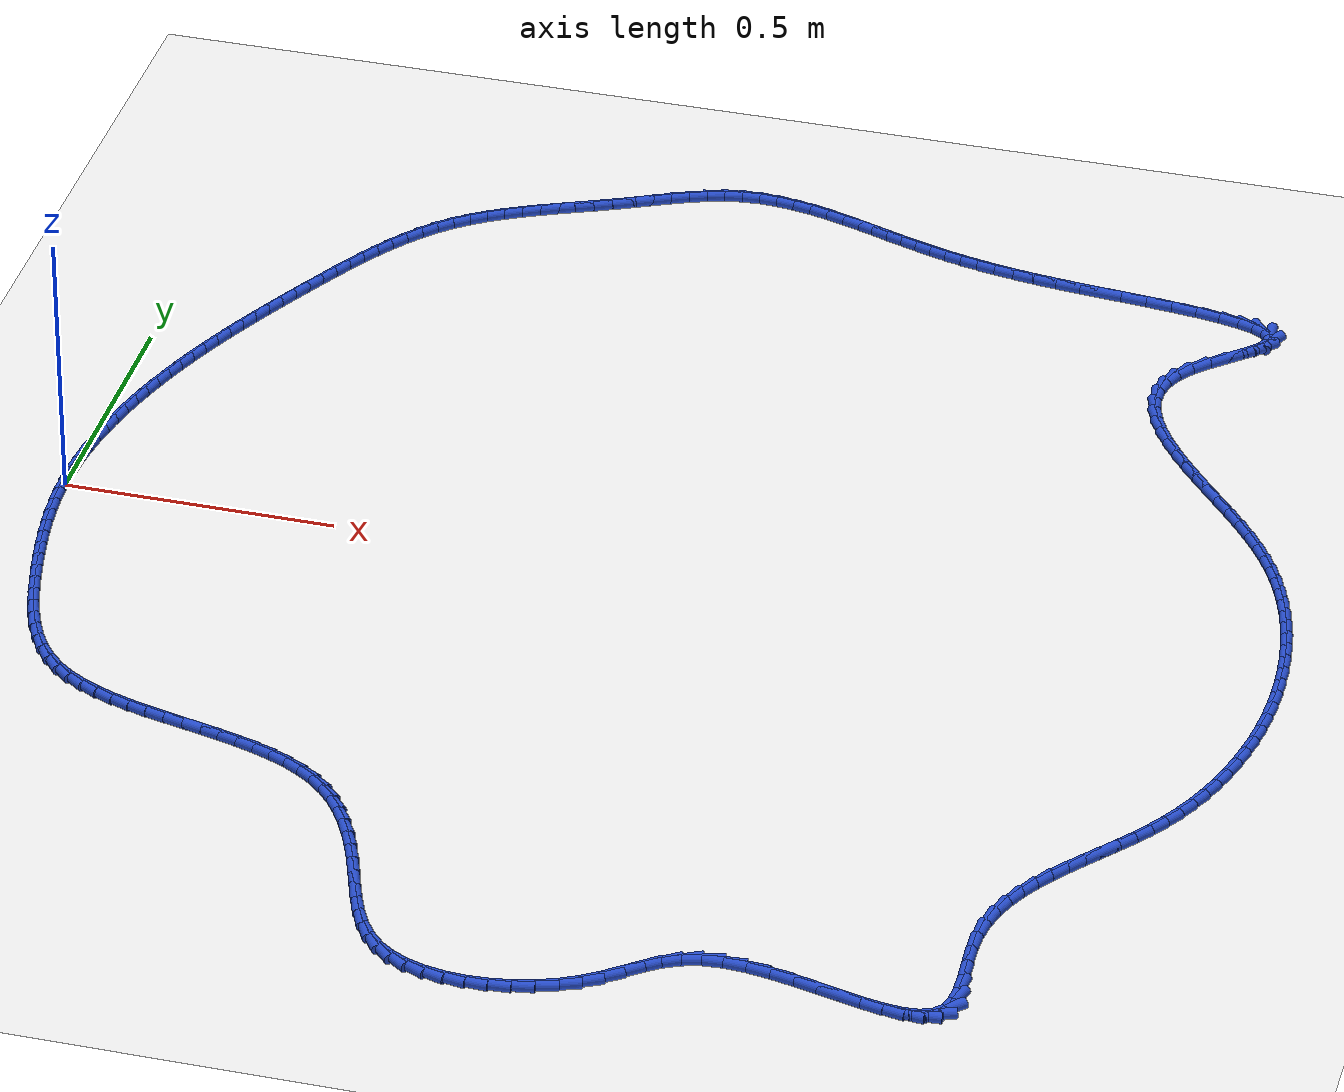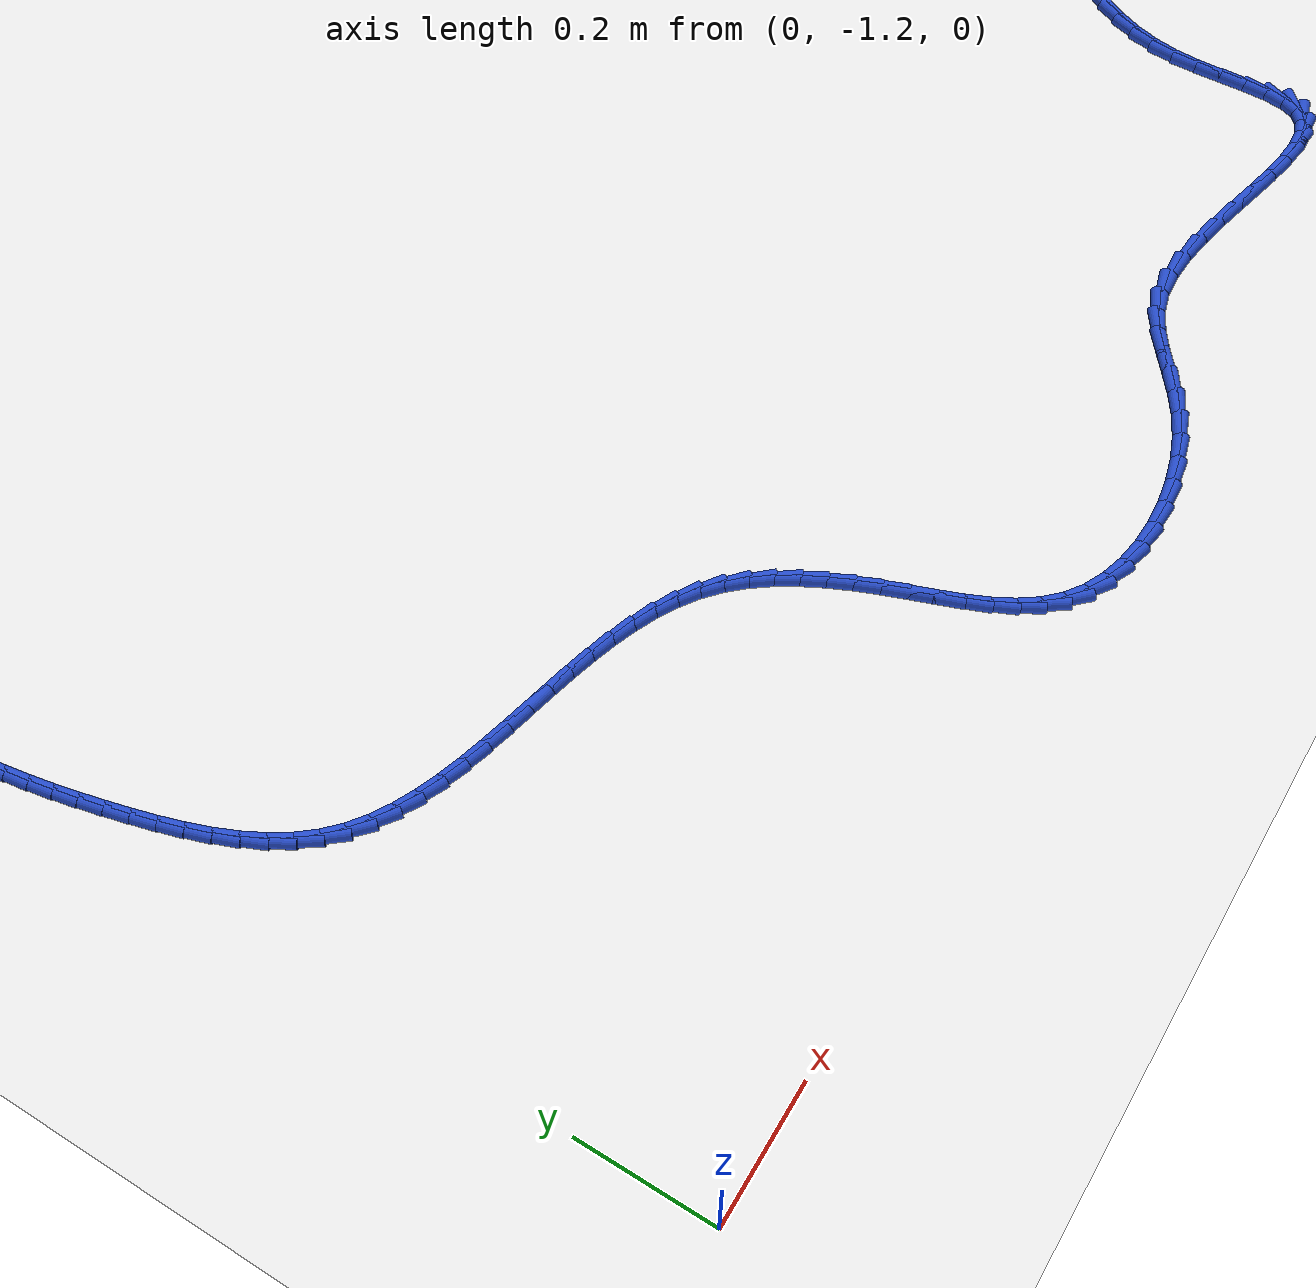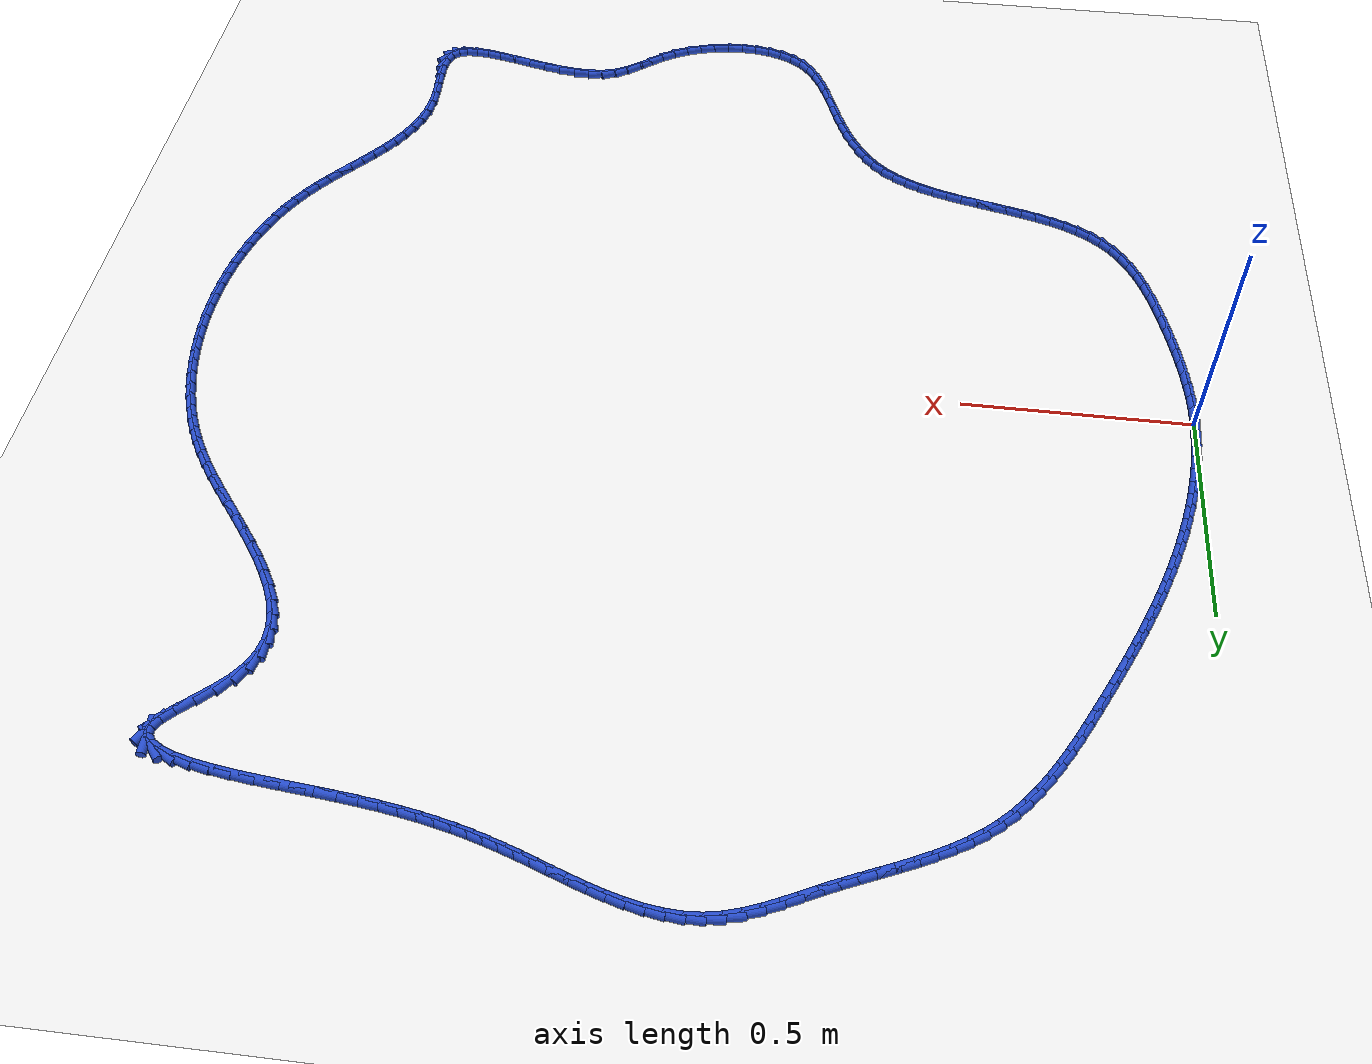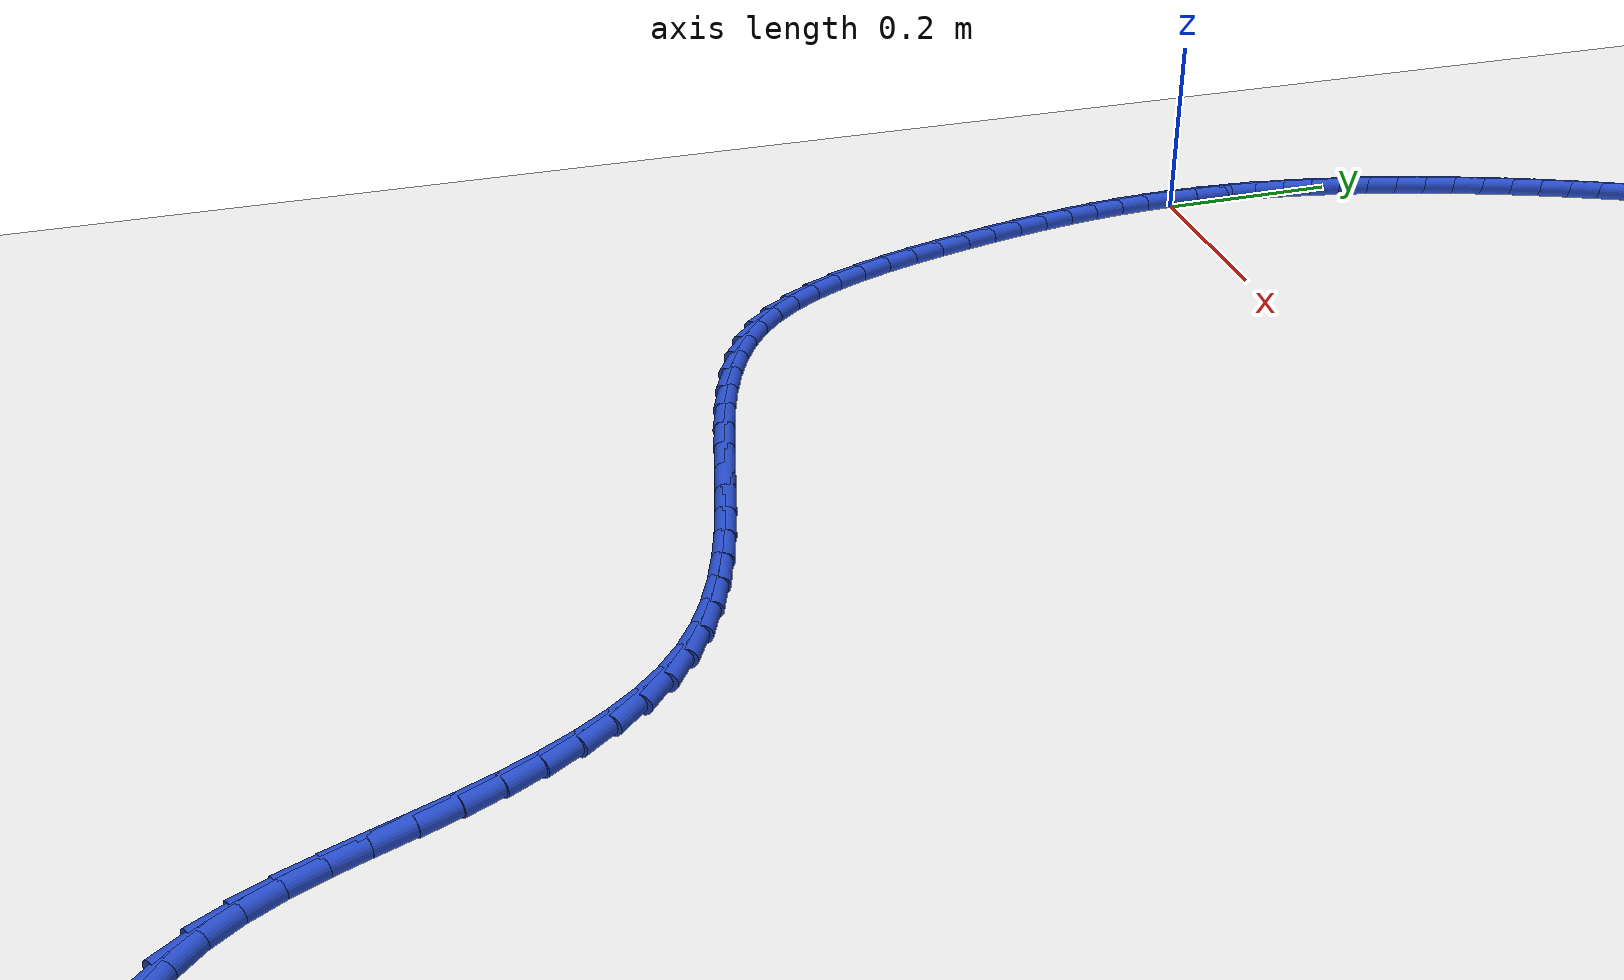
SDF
<sdf version="1.6">
 <world name="default">
  <light name="sun" type="directional">
   <pose>0 0 10 0 -0 0</pose>
   <diffuse>0.8 0.8 0.8 1</diffuse>
   <specular>0.2 0.2 0.2 1</specular>
   <attenuation>
    <range>1000</range>
    <constant>0.9</constant>
    <linear>0.01</linear>
    <quadratic>0.001</quadratic>
   </attenuation>
   <direction>-0.5 0.1 -0.9</direction>
  </light>
  <model name="ground_plane">
   <static>1</static>
   <link name="link">
    <collision name="collision">
     <geometry><plane><normal>0 0 1</normal><size>100 100</size></plane></geometry>
     <surface><friction><ode><mu>100</mu><mu2>50</mu2></ode></friction></surface>
    </collision>
    <visual name="visual">
     <cast_shadows>0</cast_shadows>
     <geometry><plane><normal>0 0 1</normal><size>100 100</size></plane></geometry>
     <material>
      <script><uri>file://media/materials/scripts/gazebo.material</uri><name>Gazebo/WhiteGlow</name></script>
     </material>
    </visual>
   </link>
  </model>
  <gravity>0 0 -9.8</gravity>
  <magnetic_field>6e-06 2.3e-05 -4.2e-05</magnetic_field>
  <atmosphere type="adiabatic"/>
  <physics name="default_physics" default="0" type="ode">
   <max_step_size>0.001</max_step_size>
   <real_time_factor>1</real_time_factor>
   <real_time_update_rate>1000</real_time_update_rate>
  </physics>
  <scene><ambient>0.4 0.4 0.4 1</ambient><background>0.7 0.7 0.7 1</background><shadows>1</shadows></scene>
  <spherical_coordinates>
   <surface_model>EARTH_WGS84</surface_model>
   <latitude_deg>0</latitude_deg>
   <longitude_deg>0</longitude_deg>
   <elevation>0</elevation>
   <heading_deg>0</heading_deg>
  </spherical_coordinates>
  <model name="line">
   <link name="link_0">
    <pose>8.673617379884035e-18 -4.85722573273506e-17 0.01 0 1.57 1.5538400042042941</pose>
    <collision name="collision">
     <geometry><cylinder><radius>0.01</radius><length>0.08</length></cylinder></geometry>
    </collision>
    <visual name="visual">
     <material>
      <script><name>Gazebo/Blue</name><uri>file://media/materials/scripts/gazebo.material</uri></script>
     </material>
     <geometry><cylinder><radius>0.01</radius><length>0.08</length></cylinder></geometry>
    </visual>
   </link>
   <link name="link_1">
    <pose>0.0005829402250927743 0.0343756349599535 0.01 0 1.57 1.5145570619126267</pose>
    <collision name="collision">
     <geometry><cylinder><radius>0.01</radius><length>0.08</length></cylinder></geometry>
    </collision>
    <visual name="visual">
     <material>
      <script><name>Gazebo/Blue</name><uri>file://media/materials/scripts/gazebo.material</uri></script>
     </material>
     <geometry><cylinder><radius>0.01</radius><length>0.08</length></cylinder></geometry>
    </visual>
   </link>
   <link name="link_2">
    <pose>0.002524983309487091 0.06887102158644641 0.01 0 1.57 1.4776652040989346</pose>
    <collision name="collision">
     <geometry><cylinder><radius>0.01</radius><length>0.08</length></cylinder></geometry>
    </collision>
    <visual name="visual">
     <material>
      <script><name>Gazebo/Blue</name><uri>file://media/materials/scripts/gazebo.material</uri></script>
     </material>
     <geometry><cylinder><radius>0.01</radius><length>0.08</length></cylinder></geometry>
    </visual>
   </link>
   <link name="link_3">
    <pose>0.00575157739655551 0.10341651051952847 0.01 0 1.57 1.4429963994550714</pose>
    <collision name="collision">
     <geometry><cylinder><radius>0.01</radius><length>0.08</length></cylinder></geometry>
    </collision>
    <visual name="visual">
     <material>
      <script><name>Gazebo/Blue</name><uri>file://media/materials/scripts/gazebo.material</uri></script>
     </material>
     <geometry><cylinder><radius>0.01</radius><length>0.08</length></cylinder></geometry>
    </visual>
   </link>
   <link name="link_4">
    <pose>0.010188170629670588 0.13794245239924952 0.01 0 1.57 1.4103815337758716</pose>
    <collision name="collision">
     <geometry><cylinder><radius>0.01</radius><length>0.08</length></cylinder></geometry>
    </collision>
    <visual name="visual">
     <material>
      <script><name>Gazebo/Blue</name><uri>file://media/materials/scripts/gazebo.material</uri></script>
     </material>
     <geometry><cylinder><radius>0.01</radius><length>0.08</length></cylinder></geometry>
    </visual>
   </link>
   <link name="link_5">
    <pose>0.015760211152204887 0.17237919786565936 0.01 0 1.57 1.3796539417783982</pose>
    <collision name="collision">
     <geometry><cylinder><radius>0.01</radius><length>0.08</length></cylinder></geometry>
    </collision>
    <visual name="visual">
     <material>
      <script><name>Gazebo/Blue</name><uri>file://media/materials/scripts/gazebo.material</uri></script>
     </material>
     <geometry><cylinder><radius>0.01</radius><length>0.08</length></cylinder></geometry>
    </visual>
   </link>
   <link name="link_6">
    <pose>0.02239314710753095 0.2066570975588077 0.01 0 1.57 1.3506516858308686</pose>
    <collision name="collision">
     <geometry><cylinder><radius>0.01</radius><length>0.08</length></cylinder></geometry>
    </collision>
    <visual name="visual">
     <material>
      <script><name>Gazebo/Blue</name><uri>file://media/materials/scripts/gazebo.material</uri></script>
     </material>
     <geometry><cylinder><radius>0.01</radius><length>0.08</length></cylinder></geometry>
    </visual>
   </link>
   <link name="link_7">
    <pose>0.03001242663902133 0.24070650211874436 0.01 0 1.57 1.3232188465926384</pose>
    <collision name="collision">
     <geometry><cylinder><radius>0.01</radius><length>0.08</length></cylinder></geometry>
    </collision>
    <visual name="visual">
     <material>
      <script><name>Gazebo/Blue</name><uri>file://media/materials/scripts/gazebo.material</uri></script>
     </material>
     <geometry><cylinder><radius>0.01</radius><length>0.08</length></cylinder></geometry>
    </visual>
   </link>
   <link name="link_8">
    <pose>0.0385434978900486 0.27445776218551926 0.01 0 1.57 1.2971913056015587</pose>
    <collision name="collision">
     <geometry><cylinder><radius>0.01</radius><length>0.08</length></cylinder></geometry>
    </collision>
    <visual name="visual">
     <material>
      <script><name>Gazebo/Blue</name><uri>file://media/materials/scripts/gazebo.material</uri></script>
     </material>
     <geometry><cylinder><radius>0.01</radius><length>0.08</length></cylinder></geometry>
    </visual>
   </link>
   <link name="link_9">
    <pose>0.04791459886889569 0.3078492776391433 0.01 0 1.57 1.2723763430447803</pose>
    <collision name="collision">
     <geometry><cylinder><radius>0.01</radius><length>0.08</length></cylinder></geometry>
    </collision>
    <visual name="visual">
     <material>
      <script><name>Gazebo/Blue</name><uri>file://media/materials/scripts/gazebo.material</uri></script>
     </material>
     <geometry><cylinder><radius>0.01</radius><length>0.08</length></cylinder></geometry>
    </visual>
   </link>
   <link name="link_10">
    <pose>0.058075743798754145 0.3408822764838835 0.01 0 1.57 1.2487791047035772</pose>
    <collision name="collision">
     <geometry><cylinder><radius>0.01</radius><length>0.08</length></cylinder></geometry>
    </collision>
    <visual name="visual">
     <material>
      <script><name>Gazebo/Blue</name><uri>file://media/materials/scripts/gazebo.material</uri></script>
     </material>
     <geometry><cylinder><radius>0.01</radius><length>0.08</length></cylinder></geometry>
    </visual>
   </link>
   <link name="link_11">
    <pose>0.06898717909080394 0.3735875083456953 0.01 0 1.57 1.2264701689379098</pose>
    <collision name="collision">
     <geometry><cylinder><radius>0.01</radius><length>0.08</length></cylinder></geometry>
    </collision>
    <visual name="visual">
     <material>
      <script><name>Gazebo/Blue</name><uri>file://media/materials/scripts/gazebo.material</uri></script>
     </material>
     <geometry><cylinder><radius>0.01</radius><length>0.08</length></cylinder></geometry>
    </visual>
   </link>
   <link name="link_12">
    <pose>0.0806092104454255 0.40599589391007224 0.01 0 1.57 1.2055088621873966</pose>
    <collision name="collision">
     <geometry><cylinder><radius>0.01</radius><length>0.08</length></cylinder></geometry>
    </collision>
    <visual name="visual">
     <material>
      <script><name>Gazebo/Blue</name><uri>file://media/materials/scripts/gazebo.material</uri></script>
     </material>
     <geometry><cylinder><radius>0.01</radius><length>0.08</length></cylinder></geometry>
    </visual>
   </link>
   <link name="link_13">
    <pose>0.09290214356299935 0.4381383538625078 0.01 0 1.57 1.1859433986664367</pose>
    <collision name="collision">
     <geometry><cylinder><radius>0.01</radius><length>0.08</length></cylinder></geometry>
    </collision>
    <visual name="visual">
     <material>
      <script><name>Gazebo/Blue</name><uri>file://media/materials/scripts/gazebo.material</uri></script>
     </material>
     <geometry><cylinder><radius>0.01</radius><length>0.08</length></cylinder></geometry>
    </visual>
   </link>
   <link name="link_14">
    <pose>0.10582628414390591 0.4700458088884954 0.01 0 1.57 1.1678115564518285</pose>
    <collision name="collision">
     <geometry><cylinder><radius>0.01</radius><length>0.08</length></cylinder></geometry>
    </collision>
    <visual name="visual">
     <material>
      <script><name>Gazebo/Blue</name><uri>file://media/materials/scripts/gazebo.material</uri></script>
     </material>
     <geometry><cylinder><radius>0.01</radius><length>0.08</length></cylinder></geometry>
    </visual>
   </link>
   <link name="link_15">
    <pose>0.1193419378885257 0.5017491796735284 0.01 0 1.57 1.1511415133986735</pose>
    <collision name="collision">
     <geometry><cylinder><radius>0.01</radius><length>0.08</length></cylinder></geometry>
    </collision>
    <visual name="visual">
     <material>
      <script><name>Gazebo/Blue</name><uri>file://media/materials/scripts/gazebo.material</uri></script>
     </material>
     <geometry><cylinder><radius>0.01</radius><length>0.08</length></cylinder></geometry>
    </visual>
   </link>
   <link name="link_16">
    <pose>0.13340941049723917 0.5332793869031002 0.01 0 1.57 1.1359527827801705</pose>
    <collision name="collision">
     <geometry><cylinder><radius>0.01</radius><length>0.08</length></cylinder></geometry>
    </collision>
    <visual name="visual">
     <material>
      <script><name>Gazebo/Blue</name><uri>file://media/materials/scripts/gazebo.material</uri></script>
     </material>
     <geometry><cylinder><radius>0.01</radius><length>0.08</length></cylinder></geometry>
    </visual>
   </link>
   <link name="link_17">
    <pose>0.1479890076704268 0.5646673512627043 0.01 0 1.57 1.1222571949077498</pose>
    <collision name="collision">
     <geometry><cylinder><radius>0.01</radius><length>0.08</length></cylinder></geometry>
    </collision>
    <visual name="visual">
     <material>
      <script><name>Gazebo/Blue</name><uri>file://media/materials/scripts/gazebo.material</uri></script>
     </material>
     <geometry><cylinder><radius>0.01</radius><length>0.08</length></cylinder></geometry>
    </visual>
   </link>
   <link name="link_18">
    <pose>0.16304103510846907 0.5959439934378342 0.01 0 1.57 1.1100598791975194</pose>
    <collision name="collision">
     <geometry><cylinder><radius>0.01</radius><length>0.08</length></cylinder></geometry>
    </collision>
    <visual name="visual">
     <material>
      <script><name>Gazebo/Blue</name><uri>file://media/materials/scripts/gazebo.material</uri></script>
     </material>
     <geometry><cylinder><radius>0.01</radius><length>0.08</length></cylinder></geometry>
    </visual>
   </link>
   <link name="link_19">
    <pose>0.17852579851174646 0.6271402341139833 0.01 0 1.57 1.099360210108544</pose>
    <collision name="collision">
     <geometry><cylinder><radius>0.01</radius><length>0.08</length></cylinder></geometry>
    </collision>
    <visual name="visual">
     <material>
      <script><name>Gazebo/Blue</name><uri>file://media/materials/scripts/gazebo.material</uri></script>
     </material>
     <geometry><cylinder><radius>0.01</radius><length>0.08</length></cylinder></geometry>
    </visual>
   </link>
   <link name="link_20">
    <pose>0.19440360358063938 0.6582869939766448 0.01 0 1.57 1.0901526892326436</pose>
    <collision name="collision">
     <geometry><cylinder><radius>0.01</radius><length>0.08</length></cylinder></geometry>
    </collision>
    <visual name="visual">
     <material>
      <script><name>Gazebo/Blue</name><uri>file://media/materials/scripts/gazebo.material</uri></script>
     </material>
     <geometry><cylinder><radius>0.01</radius><length>0.08</length></cylinder></geometry>
    </visual>
   </link>
   <link name="link_21">
    <pose>0.2106347560155283 0.6894151937113124 0.01 0 1.57 1.082427743971415</pose>
    <collision name="collision">
     <geometry><cylinder><radius>0.01</radius><length>0.08</length></cylinder></geometry>
    </collision>
    <visual name="visual">
     <material>
      <script><name>Gazebo/Blue</name><uri>file://media/materials/scripts/gazebo.material</uri></script>
     </material>
     <geometry><cylinder><radius>0.01</radius><length>0.08</length></cylinder></geometry>
    </visual>
   </link>
   <link name="link_22">
    <pose>0.2271795615167937 0.7205557540034793 0.01 0 1.57 1.076169886864451</pose>
    <collision name="collision">
     <geometry><cylinder><radius>0.01</radius><length>0.08</length></cylinder></geometry>
    </collision>
    <visual name="visual">
     <material>
      <script><name>Gazebo/Blue</name><uri>file://media/materials/scripts/gazebo.material</uri></script>
     </material>
     <geometry><cylinder><radius>0.01</radius><length>0.08</length></cylinder></geometry>
    </visual>
   </link>
   <link name="link_23">
    <pose>0.24399838453686903 0.7517395146338893 0.01 0 1.57 1.069370174484882</pose>
    <collision name="collision">
     <geometry><cylinder><radius>0.01</radius><length>0.08</length></cylinder></geometry>
    </collision>
    <visual name="visual">
     <material>
      <script><name>Gazebo/Blue</name><uri>file://media/materials/scripts/gazebo.material</uri></script>
     </material>
     <geometry><cylinder><radius>0.01</radius><length>0.08</length></cylinder></geometry>
    </visual>
   </link>
   <link name="link_24">
    <pose>0.26109771179511226 0.7829338025306554 0.01 0 1.57 1.056435618433369</pose>
    <collision name="collision">
     <geometry><cylinder><radius>0.01</radius><length>0.08</length></cylinder></geometry>
    </collision>
    <visual name="visual">
     <material>
      <script><name>Gazebo/Blue</name><uri>file://media/materials/scripts/gazebo.material</uri></script>
     </material>
     <geometry><cylinder><radius>0.01</radius><length>0.08</length></cylinder></geometry>
    </visual>
   </link>
   <link name="link_25">
    <pose>0.27861280967705626 0.813928608066145 0.01 0 1.57 1.0362772358476444</pose>
    <collision name="collision">
     <geometry><cylinder><radius>0.01</radius><length>0.08</length></cylinder></geometry>
    </collision>
    <visual name="visual">
     <material>
      <script><name>Gazebo/Blue</name><uri>file://media/materials/scripts/gazebo.material</uri></script>
     </material>
     <geometry><cylinder><radius>0.01</radius><length>0.08</length></cylinder></geometry>
    </visual>
   </link>
   <link name="link_26">
    <pose>0.2967012463463842 0.84448321085969 0.01 0 1.57 1.0086353335715534</pose>
    <collision name="collision">
     <geometry><cylinder><radius>0.01</radius><length>0.08</length></cylinder></geometry>
    </collision>
    <visual name="visual">
     <material>
      <script><name>Gazebo/Blue</name><uri>file://media/materials/scripts/gazebo.material</uri></script>
     </material>
     <geometry><cylinder><radius>0.01</radius><length>0.08</length></cylinder></geometry>
    </visual>
   </link>
   <link name="link_27">
    <pose>0.31552058996677884 0.8743568905306207 0.01 0 1.57 0.9731372006529276</pose>
    <collision name="collision">
     <geometry><cylinder><radius>0.01</radius><length>0.08</length></cylinder></geometry>
    </collision>
    <visual name="visual">
     <material>
      <script><name>Gazebo/Blue</name><uri>file://media/materials/scripts/gazebo.material</uri></script>
     </material>
     <geometry><cylinder><radius>0.01</radius><length>0.08</length></cylinder></geometry>
    </visual>
   </link>
   <link name="link_28">
    <pose>0.3352284087019234 0.9033089266982689 0.01 0 1.57 0.929334012522785</pose>
    <collision name="collision">
     <geometry><cylinder><radius>0.01</radius><length>0.08</length></cylinder></geometry>
    </collision>
    <visual name="visual">
     <material>
      <script><name>Gazebo/Blue</name><uri>file://media/materials/scripts/gazebo.material</uri></script>
     </material>
     <geometry><cylinder><radius>0.01</radius><length>0.08</length></cylinder></geometry>
    </visual>
   </link>
   <link name="link_29">
    <pose>0.35598227071550054 0.9310985989819649 0.01 0 1.57 0.8767596339352454</pose>
    <collision name="collision">
     <geometry><cylinder><radius>0.01</radius><length>0.08</length></cylinder></geometry>
    </collision>
    <visual name="visual">
     <material>
      <script><name>Gazebo/Blue</name><uri>file://media/materials/scripts/gazebo.material</uri></script>
     </material>
     <geometry><cylinder><radius>0.01</radius><length>0.08</length></cylinder></geometry>
    </visual>
   </link>
   <link name="link_30">
    <pose>0.3779397441711933 0.9574851870010399 0.01 0 1.57 0.8150209510390791</pose>
    <collision name="collision">
     <geometry><cylinder><radius>0.01</radius><length>0.08</length></cylinder></geometry>
    </collision>
    <visual name="visual">
     <material>
      <script><name>Gazebo/Blue</name><uri>file://media/materials/scripts/gazebo.material</uri></script>
     </material>
     <geometry><cylinder><radius>0.01</radius><length>0.08</length></cylinder></geometry>
    </visual>
   </link>
   <link name="link_31">
    <pose>0.40125839723268486 0.9822279703748253 0.01 0 1.57 0.7439267222304791</pose>
    <collision name="collision">
     <geometry><cylinder><radius>0.01</radius><length>0.08</length></cylinder></geometry>
    </collision>
    <visual name="visual">
     <material>
      <script><name>Gazebo/Blue</name><uri>file://media/materials/scripts/gazebo.material</uri></script>
     </material>
     <geometry><cylinder><radius>0.01</radius><length>0.08</length></cylinder></geometry>
    </visual>
   </link>
   <link name="link_32">
    <pose>0.4260957980636578 1.0050862287226519 0.01 0 1.57 0.6656174113574291</pose>
    <collision name="collision">
     <geometry><cylinder><radius>0.01</radius><length>0.08</length></cylinder></geometry>
    </collision>
    <visual name="visual">
     <material>
      <script><name>Gazebo/Blue</name><uri>file://media/materials/scripts/gazebo.material</uri></script>
     </material>
     <geometry><cylinder><radius>0.01</radius><length>0.08</length></cylinder></geometry>
    </visual>
   </link>
   <link name="link_33">
    <pose>0.45257244700495974 1.0258742483283745 0.01 0 1.57 0.5935215961432168</pose>
    <collision name="collision">
     <geometry><cylinder><radius>0.01</radius><length>0.08</length></cylinder></geometry>
    </collision>
    <visual name="visual">
     <material>
      <script><name>Gazebo/Blue</name><uri>file://media/materials/scripts/gazebo.material</uri></script>
     </material>
     <geometry><cylinder><radius>0.01</radius><length>0.08</length></cylinder></geometry>
    </visual>
   </link>
   <link name="link_34">
    <pose>0.4805688161468793 1.0447625045488709 0.01 0 1.57 0.5333702072227969</pose>
    <collision name="collision">
     <geometry><cylinder><radius>0.01</radius><length>0.08</length></cylinder></geometry>
    </collision>
    <visual name="visual">
     <material>
      <script><name>Gazebo/Blue</name><uri>file://media/materials/scripts/gazebo.material</uri></script>
     </material>
     <geometry><cylinder><radius>0.01</radius><length>0.08</length></cylinder></geometry>
    </visual>
   </link>
   <link name="link_35">
    <pose>0.5098697715785132 1.062063346928163 0.01 0 1.57 0.4852846803948754</pose>
    <collision name="collision">
     <geometry><cylinder><radius>0.01</radius><length>0.08</length></cylinder></geometry>
    </collision>
    <visual name="visual">
     <material>
      <script><name>Gazebo/Blue</name><uri>file://media/materials/scripts/gazebo.material</uri></script>
     </material>
     <geometry><cylinder><radius>0.01</radius><length>0.08</length></cylinder></geometry>
    </visual>
   </link>
   <link name="link_36">
    <pose>0.5402599329015851 1.078089490784339 0.01 0 1.57 0.44901230556782984</pose>
    <collision name="collision">
     <geometry><cylinder><radius>0.01</radius><length>0.08</length></cylinder></geometry>
    </collision>
    <visual name="visual">
     <material>
      <script><name>Gazebo/Blue</name><uri>file://media/materials/scripts/gazebo.material</uri></script>
     </material>
     <geometry><cylinder><radius>0.01</radius><length>0.08</length></cylinder></geometry>
    </visual>
   </link>
   <link name="link_37">
    <pose>0.5715239197178191 1.0931536514354858 0.01 0 1.57 0.42415045046346056</pose>
    <collision name="collision">
     <geometry><cylinder><radius>0.01</radius><length>0.08</length></cylinder></geometry>
    </collision>
    <visual name="visual">
     <material>
      <script><name>Gazebo/Blue</name><uri>file://media/materials/scripts/gazebo.material</uri></script>
     </material>
     <geometry><cylinder><radius>0.01</radius><length>0.08</length></cylinder></geometry>
    </visual>
   </link>
   <link name="link_38">
    <pose>0.603446351628939 1.107568544199691 0.01 0 1.57 0.41029324666744726</pose>
    <collision name="collision">
     <geometry><cylinder><radius>0.01</radius><length>0.08</length></cylinder></geometry>
    </collision>
    <visual name="visual">
     <material>
      <script><name>Gazebo/Blue</name><uri>file://media/materials/scripts/gazebo.material</uri></script>
     </material>
     <geometry><cylinder><radius>0.01</radius><length>0.08</length></cylinder></geometry>
    </visual>
   </link>
   <link name="link_39">
    <pose>0.6358118482366687 1.1216468843950418 0.01 0 1.57 0.4071187258648486</pose>
    <collision name="collision">
     <geometry><cylinder><radius>0.01</radius><length>0.08</length></cylinder></geometry>
    </collision>
    <visual name="visual">
     <material>
      <script><name>Gazebo/Blue</name><uri>file://media/materials/scripts/gazebo.material</uri></script>
     </material>
     <geometry><cylinder><radius>0.01</radius><length>0.08</length></cylinder></geometry>
    </visual>
   </link>
   <link name="link_40">
    <pose>0.6684050291427319 1.1357013873396256 0.01 0 1.57 0.41442895655163137</pose>
    <collision name="collision">
     <geometry><cylinder><radius>0.01</radius><length>0.08</length></cylinder></geometry>
    </collision>
    <visual name="visual">
     <material>
      <script><name>Gazebo/Blue</name><uri>file://media/materials/scripts/gazebo.material</uri></script>
     </material>
     <geometry><cylinder><radius>0.01</radius><length>0.08</length></cylinder></geometry>
    </visual>
   </link>
   <link name="link_41">
    <pose>0.7010105139488522 1.1500447683515298 0.01 0 1.57 0.4319963011172123</pose>
    <collision name="collision">
     <geometry><cylinder><radius>0.01</radius><length>0.08</length></cylinder></geometry>
    </collision>
    <visual name="visual">
     <material>
      <script><name>Gazebo/Blue</name><uri>file://media/materials/scripts/gazebo.material</uri></script>
     </material>
     <geometry><cylinder><radius>0.01</radius><length>0.08</length></cylinder></geometry>
    </visual>
   </link>
   <link name="link_42">
    <pose>0.7334147533012595 1.16498440040724 0.01 0 1.57 0.4482483865242856</pose>
    <collision name="collision">
     <geometry><cylinder><radius>0.01</radius><length>0.08</length></cylinder></geometry>
    </collision>
    <visual name="visual">
     <material>
      <script><name>Gazebo/Blue</name><uri>file://media/materials/scripts/gazebo.material</uri></script>
     </material>
     <geometry><cylinder><radius>0.01</radius><length>0.08</length></cylinder></geometry>
    </visual>
   </link>
   <link name="link_43">
    <pose>0.7655394447579693 1.1804330537298264 0.01 0 1.57 0.4438429551699167</pose>
    <collision name="collision">
     <geometry><cylinder><radius>0.01</radius><length>0.08</length></cylinder></geometry>
    </collision>
    <visual name="visual">
     <material>
      <script><name>Gazebo/Blue</name><uri>file://media/materials/scripts/gazebo.material</uri></script>
     </material>
     <geometry><cylinder><radius>0.01</radius><length>0.08</length></cylinder></geometry>
    </visual>
   </link>
   <link name="link_44">
    <pose>0.797531985464357 1.1956449868067514 0.01 0 1.57 0.41644390522369173</pose>
    <collision name="collision">
     <geometry><cylinder><radius>0.01</radius><length>0.08</length></cylinder></geometry>
    </collision>
    <visual name="visual">
     <material>
      <script><name>Gazebo/Blue</name><uri>file://media/materials/scripts/gazebo.material</uri></script>
     </material>
     <geometry><cylinder><radius>0.01</radius><length>0.08</length></cylinder></geometry>
    </visual>
   </link>
   <link name="link_45">
    <pose>0.8295611949861457 1.2098119550639115 0.01 0 1.57 0.3648963116553577</pose>
    <collision name="collision">
     <geometry><cylinder><radius>0.01</radius><length>0.08</length></cylinder></geometry>
    </collision>
    <visual name="visual">
     <material>
      <script><name>Gazebo/Blue</name><uri>file://media/materials/scripts/gazebo.material</uri></script>
     </material>
     <geometry><cylinder><radius>0.01</radius><length>0.08</length></cylinder></geometry>
    </visual>
   </link>
   <link name="link_46">
    <pose>0.8617958928890589 1.2221257139272033 0.01 0 1.57 0.28778414597842195</pose>
    <collision name="collision">
     <geometry><cylinder><radius>0.01</radius><length>0.08</length></cylinder></geometry>
    </collision>
    <visual name="visual">
     <material>
      <script><name>Gazebo/Blue</name><uri>file://media/materials/scripts/gazebo.material</uri></script>
     </material>
     <geometry><cylinder><radius>0.01</radius><length>0.08</length></cylinder></geometry>
    </visual>
   </link>
   <link name="link_47">
    <pose>0.8944048987388195 1.231778018822522 0.01 0 1.57 0.18437723854569438</pose>
    <collision name="collision">
     <geometry><cylinder><radius>0.01</radius><length>0.08</length></cylinder></geometry>
    </collision>
    <visual name="visual">
     <material>
      <script><name>Gazebo/Blue</name><uri>file://media/materials/scripts/gazebo.material</uri></script>
     </material>
     <geometry><cylinder><radius>0.01</radius><length>0.08</length></cylinder></geometry>
    </visual>
   </link>
   <link name="link_48">
    <pose>0.9275570033969005 1.2379607320021535 0.01 0 1.57 0.06461855630904617</pose>
    <collision name="collision">
     <geometry><cylinder><radius>0.01</radius><length>0.08</length></cylinder></geometry>
    </collision>
    <visual name="visual">
     <material>
      <script><name>Gazebo/Blue</name><uri>file://media/materials/scripts/gazebo.material</uri></script>
     </material>
     <geometry><cylinder><radius>0.01</radius><length>0.08</length></cylinder></geometry>
    </visual>
   </link>
   <link name="link_49">
    <pose>0.9613453811210377 1.2401471321849646 0.01 0 1.57 -0.04211946598836702</pose>
    <collision name="collision">
     <geometry><cylinder><radius>0.01</radius><length>0.08</length></cylinder></geometry>
    </collision>
    <visual name="visual">
     <material>
      <script><name>Gazebo/Blue</name><uri>file://media/materials/scripts/gazebo.material</uri></script>
     </material>
     <geometry><cylinder><radius>0.01</radius><length>0.08</length></cylinder></geometry>
    </visual>
   </link>
   <link name="link_50">
    <pose>0.9956235250748355 1.2387025006829482 0.01 0 1.57 -0.13039655362405744</pose>
    <collision name="collision">
     <geometry><cylinder><radius>0.01</radius><length>0.08</length></cylinder></geometry>
    </collision>
    <visual name="visual">
     <material>
      <script><name>Gazebo/Blue</name><uri>file://media/materials/scripts/gazebo.material</uri></script>
     </material>
     <geometry><cylinder><radius>0.01</radius><length>0.08</length></cylinder></geometry>
    </visual>
   </link>
   <link name="link_51">
    <pose>1.0301975509877506 1.2341684397409967 0.01 0 1.57 -0.20145964547790132</pose>
    <collision name="collision">
     <geometry><cylinder><radius>0.01</radius><length>0.08</length></cylinder></geometry>
    </collision>
    <visual name="visual">
     <material>
      <script><name>Gazebo/Blue</name><uri>file://media/materials/scripts/gazebo.material</uri></script>
     </material>
     <geometry><cylinder><radius>0.01</radius><length>0.08</length></cylinder></geometry>
    </visual>
   </link>
   <link name="link_52">
    <pose>1.0648735745892397 1.227086551604003 0.01 0 1.57 -0.25697279299731723</pose>
    <collision name="collision">
     <geometry><cylinder><radius>0.01</radius><length>0.08</length></cylinder></geometry>
    </collision>
    <visual name="visual">
     <material>
      <script><name>Gazebo/Blue</name><uri>file://media/materials/scripts/gazebo.material</uri></script>
     </material>
     <geometry><cylinder><radius>0.01</radius><length>0.08</length></cylinder></geometry>
    </visual>
   </link>
   <link name="link_53">
    <pose>1.0994577116087592 1.2179984385168605 0.01 0 1.57 -0.29848274733399255</pose>
    <collision name="collision">
     <geometry><cylinder><radius>0.01</radius><length>0.08</length></cylinder></geometry>
    </collision>
    <visual name="visual">
     <material>
      <script><name>Gazebo/Blue</name><uri>file://media/materials/scripts/gazebo.material</uri></script>
     </material>
     <geometry><cylinder><radius>0.01</radius><length>0.08</length></cylinder></geometry>
    </visual>
   </link>
   <link name="link_54">
    <pose>1.1337560777757665 1.207445702724462 0.01 0 1.57 -0.32713921677775787</pose>
    <collision name="collision">
     <geometry><cylinder><radius>0.01</radius><length>0.08</length></cylinder></geometry>
    </collision>
    <visual name="visual">
     <material>
      <script><name>Gazebo/Blue</name><uri>file://media/materials/scripts/gazebo.material</uri></script>
     </material>
     <geometry><cylinder><radius>0.01</radius><length>0.08</length></cylinder></geometry>
    </visual>
   </link>
   <link name="link_55">
    <pose>1.167574788819717 1.1959699464717002 0.01 0 1.57 -0.34354863885220566</pose>
    <collision name="collision">
     <geometry><cylinder><radius>0.01</radius><length>0.08</length></cylinder></geometry>
    </collision>
    <visual name="visual">
     <material>
      <script><name>Gazebo/Blue</name><uri>file://media/materials/scripts/gazebo.material</uri></script>
     </material>
     <geometry><cylinder><radius>0.01</radius><length>0.08</length></cylinder></geometry>
    </visual>
   </link>
   <link name="link_56">
    <pose>1.2007199604700678 1.1841127720034677 0.01 0 1.57 -0.3476658537428482</pose>
    <collision name="collision">
     <geometry><cylinder><radius>0.01</radius><length>0.08</length></cylinder></geometry>
    </collision>
    <visual name="visual">
     <material>
      <script><name>Gazebo/Blue</name><uri>file://media/materials/scripts/gazebo.material</uri></script>
     </material>
     <geometry><cylinder><radius>0.01</radius><length>0.08</length></cylinder></geometry>
    </visual>
   </link>
   <link name="link_57">
    <pose>1.2329977084562762 1.1724157815646574 0.01 0 1.57 -0.33922750574225047</pose>
    <collision name="collision">
     <geometry><cylinder><radius>0.01</radius><length>0.08</length></cylinder></geometry>
    </collision>
    <visual name="visual">
     <material>
      <script><name>Gazebo/Blue</name><uri>file://media/materials/scripts/gazebo.material</uri></script>
     </material>
     <geometry><cylinder><radius>0.01</radius><length>0.08</length></cylinder></geometry>
    </visual>
   </link>
   <link name="link_58">
    <pose>1.2642497009063478 1.1613879547736976 0.01 0 1.57 -0.32315328452218234</pose>
    <collision name="collision">
     <geometry><cylinder><radius>0.01</radius><length>0.08</length></cylinder></geometry>
    </collision>
    <visual name="visual">
     <material>
      <script><name>Gazebo/Blue</name><uri>file://media/materials/scripts/gazebo.material</uri></script>
     </material>
     <geometry><cylinder><radius>0.01</radius><length>0.08</length></cylinder></geometry>
    </visual>
   </link>
   <link name="link_59">
    <pose>1.2946948787774926 1.1511920884010292 0.01 0 1.57 -0.30313473608001484</pose>
    <collision name="collision">
     <geometry><cylinder><radius>0.01</radius><length>0.08</length></cylinder></geometry>
    </collision>
    <visual name="visual">
     <material>
      <script><name>Gazebo/Blue</name><uri>file://media/materials/scripts/gazebo.material</uri></script>
     </material>
     <geometry><cylinder><radius>0.01</radius><length>0.08</length></cylinder></geometry>
    </visual>
   </link>
   <link name="link_60">
    <pose>1.324779504033277 1.1417823910885698 0.01 0 1.57 -0.27986775367355027</pose>
    <collision name="collision">
     <geometry><cylinder><radius>0.01</radius><length>0.08</length></cylinder></geometry>
    </collision>
    <visual name="visual">
     <material>
      <script><name>Gazebo/Blue</name><uri>file://media/materials/scripts/gazebo.material</uri></script>
     </material>
     <geometry><cylinder><radius>0.01</radius><length>0.08</length></cylinder></geometry>
    </visual>
   </link>
   <link name="link_61">
    <pose>1.3549529662214812 1.1331102016293444 0.01 0 1.57 -0.25431632395397946</pose>
    <collision name="collision">
     <geometry><cylinder><radius>0.01</radius><length>0.08</length></cylinder></geometry>
    </collision>
    <visual name="visual">
     <material>
      <script><name>Gazebo/Blue</name><uri>file://media/materials/scripts/gazebo.material</uri></script>
     </material>
     <geometry><cylinder><radius>0.01</radius><length>0.08</length></cylinder></geometry>
    </visual>
   </link>
   <link name="link_62">
    <pose>1.3856646548898843 1.1251268588163785 0.01 0 1.57 -0.22763532488439442</pose>
    <collision name="collision">
     <geometry><cylinder><radius>0.01</radius><length>0.08</length></cylinder></geometry>
    </collision>
    <visual name="visual">
     <material>
      <script><name>Gazebo/Blue</name><uri>file://media/materials/scripts/gazebo.material</uri></script>
     </material>
     <geometry><cylinder><radius>0.01</radius><length>0.08</length></cylinder></geometry>
    </visual>
   </link>
   <link name="link_63">
    <pose>1.417363959586269 1.117783701442698 0.01 0 1.57 -0.20100190012955987</pose>
    <collision name="collision">
     <geometry><cylinder><radius>0.01</radius><length>0.08</length></cylinder></geometry>
    </collision>
    <visual name="visual">
     <material>
      <script><name>Gazebo/Blue</name><uri>file://media/materials/scripts/gazebo.material</uri></script>
     </material>
     <geometry><cylinder><radius>0.01</radius><length>0.08</length></cylinder></geometry>
    </visual>
   </link>
   <link name="link_64">
    <pose>1.4505002698584124 1.1110320683013268 0.01 0 1.57 -0.1754555313381318</pose>
    <collision name="collision">
     <geometry><cylinder><radius>0.01</radius><length>0.08</length></cylinder></geometry>
    </collision>
    <visual name="visual">
     <material>
      <script><name>Gazebo/Blue</name><uri>file://media/materials/scripts/gazebo.material</uri></script>
     </material>
     <geometry><cylinder><radius>0.01</radius><length>0.08</length></cylinder></geometry>
    </visual>
   </link>
   <link name="link_65">
    <pose>1.485522975254097 1.1048232981852917 0.01 0 1.57 -0.1517891369159384</pose>
    <collision name="collision">
     <geometry><cylinder><radius>0.01</radius><length>0.08</length></cylinder></geometry>
    </collision>
    <visual name="visual">
     <material>
      <script><name>Gazebo/Blue</name><uri>file://media/materials/scripts/gazebo.material</uri></script>
     </material>
     <geometry><cylinder><radius>0.01</radius><length>0.08</length></cylinder></geometry>
    </visual>
   </link>
   <link name="link_66">
    <pose>1.5228814653211022 1.0991087298876177 0.01 0 1.57 -0.13050823900713504</pose>
    <collision name="collision">
     <geometry><cylinder><radius>0.01</radius><length>0.08</length></cylinder></geometry>
    </collision>
    <visual name="visual">
     <material>
      <script><name>Gazebo/Blue</name><uri>file://media/materials/scripts/gazebo.material</uri></script>
     </material>
     <geometry><cylinder><radius>0.01</radius><length>0.08</length></cylinder></geometry>
    </visual>
   </link>
   <link name="link_67">
    <pose>1.5630251296072082 1.0938397022013298 0.01 0 1.57 -0.11186192257931665</pose>
    <collision name="collision">
     <geometry><cylinder><radius>0.01</radius><length>0.08</length></cylinder></geometry>
    </collision>
    <visual name="visual">
     <material>
      <script><name>Gazebo/Blue</name><uri>file://media/materials/scripts/gazebo.material</uri></script>
     </material>
     <geometry><cylinder><radius>0.01</radius><length>0.08</length></cylinder></geometry>
    </visual>
   </link>
   <link name="link_68">
    <pose>1.6064009562803203 1.0889672587549828 0.01 0 1.57 -0.09833792175328127</pose>
    <collision name="collision">
     <geometry><cylinder><radius>0.01</radius><length>0.08</length></cylinder></geometry>
    </collision>
    <visual name="visual">
     <material>
      <script><name>Gazebo/Blue</name><uri>file://media/materials/scripts/gazebo.material</uri></script>
     </material>
     <geometry><cylinder><radius>0.01</radius><length>0.08</length></cylinder></geometry>
    </visual>
   </link>
   <link name="link_69">
    <pose>1.652925868564802 1.0843772904954798 0.01 0 1.57 -0.09411084288754398</pose>
    <collision name="collision">
     <geometry><cylinder><radius>0.01</radius><length>0.08</length></cylinder></geometry>
    </collision>
    <visual name="visual">
     <material>
      <script><name>Gazebo/Blue</name><uri>file://media/materials/scripts/gazebo.material</uri></script>
     </material>
     <geometry><cylinder><radius>0.01</radius><length>0.08</length></cylinder></geometry>
    </visual>
   </link>
   <link name="link_70">
    <pose>1.7013236756732426 1.0798090373256772 0.01 0 1.57 -0.09853709206916762</pose>
    <collision name="collision">
     <geometry><cylinder><radius>0.01</radius><length>0.08</length></cylinder></geometry>
    </collision>
    <visual name="visual">
     <material>
      <script><name>Gazebo/Blue</name><uri>file://media/materials/scripts/gazebo.material</uri></script>
     </material>
     <geometry><cylinder><radius>0.01</radius><length>0.08</length></cylinder></geometry>
    </visual>
   </link>
   <link name="link_71">
    <pose>1.75015511558953 1.0749816953255387 0.01 0 1.57 -0.11175704303943458</pose>
    <collision name="collision">
     <geometry><cylinder><radius>0.01</radius><length>0.08</length></cylinder></geometry>
    </collision>
    <visual name="visual">
     <material>
      <script><name>Gazebo/Blue</name><uri>file://media/materials/scripts/gazebo.material</uri></script>
     </material>
     <geometry><cylinder><radius>0.01</radius><length>0.08</length></cylinder></geometry>
    </visual>
   </link>
   <link name="link_72">
    <pose>1.7979809262975561 1.0696144605750273 0.01 0 1.57 -0.13551958454028964</pose>
    <collision name="collision">
     <geometry><cylinder><radius>0.01</radius><length>0.08</length></cylinder></geometry>
    </collision>
    <visual name="visual">
     <material>
      <script><name>Gazebo/Blue</name><uri>file://media/materials/scripts/gazebo.material</uri></script>
     </material>
     <geometry><cylinder><radius>0.01</radius><length>0.08</length></cylinder></geometry>
    </visual>
   </link>
   <link name="link_73">
    <pose>1.8433618457812093 1.0634265291541072 0.01 0 1.57 -0.17388855542265794</pose>
    <collision name="collision">
     <geometry><cylinder><radius>0.01</radius><length>0.08</length></cylinder></geometry>
    </collision>
    <visual name="visual">
     <material>
      <script><name>Gazebo/Blue</name><uri>file://media/materials/scripts/gazebo.material</uri></script>
     </material>
     <geometry><cylinder><radius>0.01</radius><length>0.08</length></cylinder></geometry>
    </visual>
   </link>
   <link name="link_74">
    <pose>1.8848586120243795 1.0561370971427415 0.01 0 1.57 -0.23528703205506363</pose>
    <collision name="collision">
     <geometry><cylinder><radius>0.01</radius><length>0.08</length></cylinder></geometry>
    </collision>
    <visual name="visual">
     <material>
      <script><name>Gazebo/Blue</name><uri>file://media/materials/scripts/gazebo.material</uri></script>
     </material>
     <geometry><cylinder><radius>0.01</radius><length>0.08</length></cylinder></geometry>
    </visual>
   </link>
   <link name="link_75">
    <pose>1.921031963010957 1.0474653606208941 0.01 0 1.57 -0.33791949946959987</pose>
    <collision name="collision">
     <geometry><cylinder><radius>0.01</radius><length>0.08</length></cylinder></geometry>
    </collision>
    <visual name="visual">
     <material>
      <script><name>Gazebo/Blue</name><uri>file://media/materials/scripts/gazebo.material</uri></script>
     </material>
     <geometry><cylinder><radius>0.01</radius><length>0.08</length></cylinder></geometry>
    </visual>
   </link>
   <link name="link_76">
    <pose>1.9504426367248309 1.0371305156685284 0.01 0 1.57 -0.5247963479720211</pose>
    <collision name="collision">
     <geometry><cylinder><radius>0.01</radius><length>0.08</length></cylinder></geometry>
    </collision>
    <visual name="visual">
     <material>
      <script><name>Gazebo/Blue</name><uri>file://media/materials/scripts/gazebo.material</uri></script>
     </material>
     <geometry><cylinder><radius>0.01</radius><length>0.08</length></cylinder></geometry>
    </visual>
   </link>
   <link name="link_77">
    <pose>1.9716513711498922 1.024851758365609 0.01 0 1.57 -0.8975389460871354</pose>
    <collision name="collision">
     <geometry><cylinder><radius>0.01</radius><length>0.08</length></cylinder></geometry>
    </collision>
    <visual name="visual">
     <material>
      <script><name>Gazebo/Blue</name><uri>file://media/materials/scripts/gazebo.material</uri></script>
     </material>
     <geometry><cylinder><radius>0.01</radius><length>0.08</length></cylinder></geometry>
    </visual>
   </link>
   <link name="link_78">
    <pose>1.9832189042700286 1.0103482847920975 0.01 0 1.57 -1.5421681354130943</pose>
    <collision name="collision">
     <geometry><cylinder><radius>0.01</radius><length>0.08</length></cylinder></geometry>
    </collision>
    <visual name="visual">
     <material>
      <script><name>Gazebo/Blue</name><uri>file://media/materials/scripts/gazebo.material</uri></script>
     </material>
     <geometry><cylinder><radius>0.01</radius><length>0.08</length></cylinder></geometry>
    </visual>
   </link>
   <link name="link_79">
    <pose>1.983705974069132 0.9933392910279593 0.01 0 1.57 1.036733792310136</pose>
    <collision name="collision">
     <geometry><cylinder><radius>0.01</radius><length>0.08</length></cylinder></geometry>
    </collision>
    <visual name="visual">
     <material>
      <script><name>Gazebo/Blue</name><uri>file://media/materials/scripts/gazebo.material</uri></script>
     </material>
     <geometry><cylinder><radius>0.01</radius><length>0.08</length></cylinder></geometry>
    </visual>
   </link>
   <link name="link_80">
    <pose>1.972024787380126 0.9735871126189519 0.01 0 1.57 0.8015503148508597</pose>
    <collision name="collision">
     <geometry><cylinder><radius>0.01</radius><length>0.08</length></cylinder></geometry>
    </collision>
    <visual name="visual">
     <material>
      <script><name>Gazebo/Blue</name><uri>file://media/materials/scripts/gazebo.material</uri></script>
     </material>
     <geometry><cylinder><radius>0.01</radius><length>0.08</length></cylinder></geometry>
    </visual>
   </link>
   <link name="link_81">
    <pose>1.950409270121253 0.9512617946055867 0.01 0 1.57 0.7280766279803434</pose>
    <collision name="collision">
     <geometry><cylinder><radius>0.01</radius><length>0.08</length></cylinder></geometry>
    </collision>
    <visual name="visual">
     <material>
      <script><name>Gazebo/Blue</name><uri>file://media/materials/scripts/gazebo.material</uri></script>
     </material>
     <geometry><cylinder><radius>0.01</radius><length>0.08</length></cylinder></geometry>
    </visual>
   </link>
   <link name="link_82">
    <pose>1.9229217804021126 0.9267578047281213 0.01 0 1.57 0.7315981496491821</pose>
    <collision name="collision">
     <geometry><cylinder><radius>0.01</radius><length>0.08</length></cylinder></geometry>
    </collision>
    <visual name="visual">
     <material>
      <script><name>Gazebo/Blue</name><uri>file://media/materials/scripts/gazebo.material</uri></script>
     </material>
     <geometry><cylinder><radius>0.01</radius><length>0.08</length></cylinder></geometry>
    </visual>
   </link>
   <link name="link_83">
    <pose>1.8936436916379966 0.9004719446751321 0.01 0 1.57 0.79790457537912</pose>
    <collision name="collision">
     <geometry><cylinder><radius>0.01</radius><length>0.08</length></cylinder></geometry>
    </collision>
    <visual name="visual">
     <material>
      <script><name>Gazebo/Blue</name><uri>file://media/materials/scripts/gazebo.material</uri></script>
     </material>
     <geometry><cylinder><radius>0.01</radius><length>0.08</length></cylinder></geometry>
    </visual>
   </link>
   <link name="link_84">
    <pose>1.8666563772441975 0.8728010161351973 0.01 0 1.57 0.9437957365544334</pose>
    <collision name="collision">
     <geometry><cylinder><radius>0.01</radius><length>0.08</length></cylinder></geometry>
    </collision>
    <visual name="visual">
     <material>
      <script><name>Gazebo/Blue</name><uri>file://media/materials/scripts/gazebo.material</uri></script>
     </material>
     <geometry><cylinder><radius>0.01</radius><length>0.08</length></cylinder></geometry>
    </visual>
   </link>
   <link name="link_85">
    <pose>1.8458844515930222 0.8441315308642866 0.01 0 1.57 1.1508885292522815</pose>
    <collision name="collision">
     <geometry><cylinder><radius>0.01</radius><length>0.08</length></cylinder></geometry>
    </collision>
    <visual name="visual">
     <material>
      <script><name>Gazebo/Blue</name><uri>file://media/materials/scripts/gazebo.material</uri></script>
     </material>
     <geometry><cylinder><radius>0.01</radius><length>0.08</length></cylinder></geometry>
    </visual>
   </link>
   <link name="link_86">
    <pose>1.832737660106028 0.8146849203045082 0.01 0 1.57 1.3698549419162098</pose>
    <collision name="collision">
     <geometry><cylinder><radius>0.01</radius><length>0.08</length></cylinder></geometry>
    </collision>
    <visual name="visual">
     <material>
      <script><name>Gazebo/Blue</name><uri>file://media/materials/scripts/gazebo.material</uri></script>
     </material>
     <geometry><cylinder><radius>0.01</radius><length>0.08</length></cylinder></geometry>
    </visual>
   </link>
   <link name="link_87">
    <pose>1.826599388398795 0.7845496021627316 0.01 0 1.57 -1.564419989657227</pose>
    <collision name="collision">
     <geometry><cylinder><radius>0.01</radius><length>0.08</length></cylinder></geometry>
    </collision>
    <visual name="visual">
     <material>
      <script><name>Gazebo/Blue</name><uri>file://media/materials/scripts/gazebo.material</uri></script>
     </material>
     <geometry><cylinder><radius>0.01</radius><length>0.08</length></cylinder></geometry>
    </visual>
   </link>
   <link name="link_88">
    <pose>1.826795395773758 0.7538102114557363 0.01 0 1.57 -1.385602425796157</pose>
    <collision name="collision">
     <geometry><cylinder><radius>0.01</radius><length>0.08</length></cylinder></geometry>
    </collision>
    <visual name="visual">
     <material>
      <script><name>Gazebo/Blue</name><uri>file://media/materials/scripts/gazebo.material</uri></script>
     </material>
     <geometry><cylinder><radius>0.01</radius><length>0.08</length></cylinder></geometry>
    </visual>
   </link>
   <link name="link_89">
    <pose>1.8326514415333535 0.7225513832003012 0.01 0 1.57 -1.2411921001665407</pose>
    <collision name="collision">
     <geometry><cylinder><radius>0.01</radius><length>0.08</length></cylinder></geometry>
    </collision>
    <visual name="visual">
     <material>
      <script><name>Gazebo/Blue</name><uri>file://media/materials/scripts/gazebo.material</uri></script>
     </material>
     <geometry><cylinder><radius>0.01</radius><length>0.08</length></cylinder></geometry>
    </visual>
   </link>
   <link name="link_90">
    <pose>1.8434932849800165 0.6908577524132057 0.01 0 1.57 -1.129065646686271</pose>
    <collision name="collision">
     <geometry><cylinder><radius>0.01</radius><length>0.08</length></cylinder></geometry>
    </collision>
    <visual name="visual">
     <material>
      <script><name>Gazebo/Blue</name><uri>file://media/materials/scripts/gazebo.material</uri></script>
     </material>
     <geometry><cylinder><radius>0.01</radius><length>0.08</length></cylinder></geometry>
    </visual>
   </link>
   <link name="link_91">
    <pose>1.8586466854161827 0.6588139541112281 0.01 0 1.57 -1.0440251396247462</pose>
    <collision name="collision">
     <geometry><cylinder><radius>0.01</radius><length>0.08</length></cylinder></geometry>
    </collision>
    <visual name="visual">
     <material>
      <script><name>Gazebo/Blue</name><uri>file://media/materials/scripts/gazebo.material</uri></script>
     </material>
     <geometry><cylinder><radius>0.01</radius><length>0.08</length></cylinder></geometry>
    </visual>
   </link>
   <link name="link_92">
    <pose>1.8774374021442877 0.6265046233111485 0.01 0 1.57 -0.9808010754879626</pose>
    <collision name="collision">
     <geometry><cylinder><radius>0.01</radius><length>0.08</length></cylinder></geometry>
    </collision>
    <visual name="visual">
     <material>
      <script><name>Gazebo/Blue</name><uri>file://media/materials/scripts/gazebo.material</uri></script>
     </material>
     <geometry><cylinder><radius>0.01</radius><length>0.08</length></cylinder></geometry>
    </visual>
   </link>
   <link name="link_93">
    <pose>1.8991911944667663 0.594014395029745 0.01 0 1.57 -0.9351428031789258</pose>
    <collision name="collision">
     <geometry><cylinder><radius>0.01</radius><length>0.08</length></cylinder></geometry>
    </collision>
    <visual name="visual">
     <material>
      <script><name>Gazebo/Blue</name><uri>file://media/materials/scripts/gazebo.material</uri></script>
     </material>
     <geometry><cylinder><radius>0.01</radius><length>0.08</length></cylinder></geometry>
    </visual>
   </link>
   <link name="link_94">
    <pose>1.9232338216860543 0.5614279042837972 0.01 0 1.57 -0.9039852305204067</pose>
    <collision name="collision">
     <geometry><cylinder><radius>0.01</radius><length>0.08</length></cylinder></geometry>
    </collision>
    <visual name="visual">
     <material>
      <script><name>Gazebo/Blue</name><uri>file://media/materials/scripts/gazebo.material</uri></script>
     </material>
     <geometry><cylinder><radius>0.01</radius><length>0.08</length></cylinder></geometry>
    </visual>
   </link>
   <link name="link_95">
    <pose>1.9488910431045885 0.5288297860900839 0.01 0 1.57 -0.8853224809207515</pose>
    <collision name="collision">
     <geometry><cylinder><radius>0.01</radius><length>0.08</length></cylinder></geometry>
    </collision>
    <visual name="visual">
     <material>
      <script><name>Gazebo/Blue</name><uri>file://media/materials/scripts/gazebo.material</uri></script>
     </material>
     <geometry><cylinder><radius>0.01</radius><length>0.08</length></cylinder></geometry>
    </visual>
   </link>
   <link name="link_96">
    <pose>1.9754886180248028 0.49630467546538487 0.01 0 1.57 -0.8780524695200574</pose>
    <collision name="collision">
     <geometry><cylinder><radius>0.01</radius><length>0.08</length></cylinder></geometry>
    </collision>
    <visual name="visual">
     <material>
      <script><name>Gazebo/Blue</name><uri>file://media/materials/scripts/gazebo.material</uri></script>
     </material>
     <geometry><cylinder><radius>0.01</radius><length>0.08</length></cylinder></geometry>
    </visual>
   </link>
   <link name="link_97">
    <pose>2.0023523057491333 0.46393720742647837 0.01 0 1.57 -0.8818808299381252</pose>
    <collision name="collision">
     <geometry><cylinder><radius>0.01</radius><length>0.08</length></cylinder></geometry>
    </collision>
    <visual name="visual">
     <material>
      <script><name>Gazebo/Blue</name><uri>file://media/materials/scripts/gazebo.material</uri></script>
     </material>
     <geometry><cylinder><radius>0.01</radius><length>0.08</length></cylinder></geometry>
    </visual>
   </link>
   <link name="link_98">
    <pose>2.028807865580015 0.43181201699014327 0.01 0 1.57 -0.8973113338929862</pose>
    <collision name="collision">
     <geometry><cylinder><radius>0.01</radius><length>0.08</length></cylinder></geometry>
    </collision>
    <visual name="visual">
     <material>
      <script><name>Gazebo/Blue</name><uri>file://media/materials/scripts/gazebo.material</uri></script>
     </material>
     <geometry><cylinder><radius>0.01</radius><length>0.08</length></cylinder></geometry>
    </visual>
   </link>
   <link name="link_99">
    <pose>2.0541810568198837 0.4000137391731597 0.01 0 1.57 -0.9257364491080634</pose>
    <collision name="collision">
     <geometry><cylinder><radius>0.01</radius><length>0.08</length></cylinder></geometry>
    </collision>
    <visual name="visual">
     <material>
      <script><name>Gazebo/Blue</name><uri>file://media/materials/scripts/gazebo.material</uri></script>
     </material>
     <geometry><cylinder><radius>0.01</radius><length>0.08</length></cylinder></geometry>
    </visual>
   </link>
   <link name="link_100">
    <pose>2.0777976387711754 0.3686270089923055 0.01 0 1.57 -0.9677758737793485</pose>
    <collision name="collision">
     <geometry><cylinder><radius>0.01</radius><length>0.08</length></cylinder></geometry>
    </collision>
    <visual name="visual">
     <material>
      <script><name>Gazebo/Blue</name><uri>file://media/materials/scripts/gazebo.material</uri></script>
     </material>
     <geometry><cylinder><radius>0.01</radius><length>0.08</length></cylinder></geometry>
    </visual>
   </link>
   <link name="link_101">
    <pose>2.0990948003103984 0.33769791343273337 0.01 0 1.57 -1.0158702733502711</pose>
    <collision name="collision">
     <geometry><cylinder><radius>0.01</radius><length>0.08</length></cylinder></geometry>
    </collision>
    <visual name="visual">
     <material>
      <script><name>Gazebo/Blue</name><uri>file://media/materials/scripts/gazebo.material</uri></script>
     </material>
     <geometry><cylinder><radius>0.01</radius><length>0.08</length></cylinder></geometry>
    </visual>
   </link>
   <link name="link_102">
    <pose>2.1180773163286886 0.30707618834189 0.01 0 1.57 -1.0663683195461382</pose>
    <collision name="collision">
     <geometry><cylinder><radius>0.01</radius><length>0.08</length></cylinder></geometry>
    </collision>
    <visual name="visual">
     <material>
      <script><name>Gazebo/Blue</name><uri>file://media/materials/scripts/gazebo.material</uri></script>
     </material>
     <geometry><cylinder><radius>0.01</radius><length>0.08</length></cylinder></geometry>
    </visual>
   </link>
   <link name="link_103">
    <pose>2.1349302232884564 0.2765492097421198 0.01 0 1.57 -1.1180155432965773</pose>
    <collision name="collision">
     <geometry><cylinder><radius>0.01</radius><length>0.08</length></cylinder></geometry>
    </collision>
    <visual name="visual">
     <material>
      <script><name>Gazebo/Blue</name><uri>file://media/materials/scripts/gazebo.material</uri></script>
     </material>
     <geometry><cylinder><radius>0.01</radius><length>0.08</length></cylinder></geometry>
    </visual>
   </link>
   <link name="link_104">
    <pose>2.149838631728487 0.24590432802972664 0.01 0 1.57 -1.1693506676141914</pose>
    <collision name="collision">
     <geometry><cylinder><radius>0.01</radius><length>0.08</length></cylinder></geometry>
    </collision>
    <visual name="visual">
     <material>
      <script><name>Gazebo/Blue</name><uri>file://media/materials/scripts/gazebo.material</uri></script>
     </material>
     <geometry><cylinder><radius>0.01</radius><length>0.08</length></cylinder></geometry>
    </visual>
   </link>
   <link name="link_105">
    <pose>2.1629876521875686 0.21492889360101647 0.01 0 1.57 -1.2188507446436363</pose>
    <collision name="collision">
     <geometry><cylinder><radius>0.01</radius><length>0.08</length></cylinder></geometry>
    </collision>
    <visual name="visual">
     <material>
      <script><name>Gazebo/Blue</name><uri>file://media/materials/scripts/gazebo.material</uri></script>
     </material>
     <geometry><cylinder><radius>0.01</radius><length>0.08</length></cylinder></geometry>
    </visual>
   </link>
   <link name="link_106">
    <pose>2.174562395204489 0.18341025685229337 0.01 0 1.57 -1.2651147756694412</pose>
    <collision name="collision">
     <geometry><cylinder><radius>0.01</radius><length>0.08</length></cylinder></geometry>
    </collision>
    <visual name="visual">
     <material>
      <script><name>Gazebo/Blue</name><uri>file://media/materials/scripts/gazebo.material</uri></script>
     </material>
     <geometry><cylinder><radius>0.01</radius><length>0.08</length></cylinder></geometry>
    </visual>
   </link>
   <link name="link_107">
    <pose>2.184746745264723 0.15113763995014962 0.01 0 1.57 -1.3082467776544147</pose>
    <collision name="collision">
     <geometry><cylinder><radius>0.01</radius><length>0.08</length></cylinder></geometry>
    </collision>
    <visual name="visual">
     <material>
      <script><name>Gazebo/Blue</name><uri>file://media/materials/scripts/gazebo.material</uri></script>
     </material>
     <geometry><cylinder><radius>0.01</radius><length>0.08</length></cylinder></geometry>
    </visual>
   </link>
   <link name="link_108">
    <pose>2.1936479638212907 0.1180172426136008 0.01 0 1.57 -1.3499804614221427</pose>
    <collision name="collision">
     <geometry><cylinder><radius>0.01</radius><length>0.08</length></cylinder></geometry>
    </collision>
    <visual name="visual">
     <material>
      <script><name>Gazebo/Blue</name><uri>file://media/materials/scripts/gazebo.material</uri></script>
     </material>
     <geometry><cylinder><radius>0.01</radius><length>0.08</length></cylinder></geometry>
    </visual>
   </link>
   <link name="link_109">
    <pose>2.2012527529903867 0.08413931804652125 0.01 0 1.57 -1.3907614188943616</pose>
    <collision name="collision">
     <geometry><cylinder><radius>0.01</radius><length>0.08</length></cylinder></geometry>
    </collision>
    <visual name="visual">
     <material>
      <script><name>Gazebo/Blue</name><uri>file://media/materials/scripts/gazebo.material</uri></script>
     </material>
     <geometry><cylinder><radius>0.01</radius><length>0.08</length></cylinder></geometry>
    </visual>
   </link>
   <link name="link_110">
    <pose>2.2075372316871347 0.0496102764348032 0.01 0 1.57 -1.4308626383242748</pose>
    <collision name="collision">
     <geometry><cylinder><radius>0.01</radius><length>0.08</length></cylinder></geometry>
    </collision>
    <visual name="visual">
     <material>
      <script><name>Gazebo/Blue</name><uri>file://media/materials/scripts/gazebo.material</uri></script>
     </material>
     <geometry><cylinder><radius>0.01</radius><length>0.08</length></cylinder></geometry>
    </visual>
   </link>
   <link name="link_111">
    <pose>2.2124775188266614 0.014536527964340728 0.01 0 1.57 -1.4705419366321162</pose>
    <collision name="collision">
     <geometry><cylinder><radius>0.01</radius><length>0.08</length></cylinder></geometry>
    </collision>
    <visual name="visual">
     <material>
      <script><name>Gazebo/Blue</name><uri>file://media/materials/scripts/gazebo.material</uri></script>
     </material>
     <geometry><cylinder><radius>0.01</radius><length>0.08</length></cylinder></geometry>
    </visual>
   </link>
   <link name="link_112">
    <pose>2.2160497333240925 -0.020975517178973453 0.01 0 1.57 -1.5100446810812649</pose>
    <collision name="collision">
     <geometry><cylinder><radius>0.01</radius><length>0.08</length></cylinder></geometry>
    </collision>
    <visual name="visual">
     <material>
      <script><name>Gazebo/Blue</name><uri>file://media/materials/scripts/gazebo.material</uri></script>
     </material>
     <geometry><cylinder><radius>0.01</radius><length>0.08</length></cylinder></geometry>
    </visual>
   </link>
   <link name="link_113">
    <pose>2.2182299940945525 -0.05681944880924618 0.01 0 1.57 -1.5496063049563849</pose>
    <collision name="collision">
     <geometry><cylinder><radius>0.01</radius><length>0.08</length></cylinder></geometry>
    </collision>
    <visual name="visual">
     <material>
      <script><name>Gazebo/Blue</name><uri>file://media/materials/scripts/gazebo.material</uri></script>
     </material>
     <geometry><cylinder><radius>0.01</radius><length>0.08</length></cylinder></geometry>
    </visual>
   </link>
   <link name="link_114">
    <pose>2.218994420053168 -0.09288885674058513 0.01 0 1.57 1.5521381326713917</pose>
    <collision name="collision">
     <geometry><cylinder><radius>0.01</radius><length>0.08</length></cylinder></geometry>
    </collision>
    <visual name="visual">
     <material>
      <script><name>Gazebo/Blue</name><uri>file://media/materials/scripts/gazebo.material</uri></script>
     </material>
     <geometry><cylinder><radius>0.01</radius><length>0.08</length></cylinder></geometry>
    </visual>
   </link>
   <link name="link_115">
    <pose>2.218319130115064 -0.12907733078709543 0.01 0 1.57 1.511781503903496</pose>
    <collision name="collision">
     <geometry><cylinder><radius>0.01</radius><length>0.08</length></cylinder></geometry>
    </collision>
    <visual name="visual">
     <material>
      <script><name>Gazebo/Blue</name><uri>file://media/materials/scripts/gazebo.material</uri></script>
     </material>
     <geometry><cylinder><radius>0.01</radius><length>0.08</length></cylinder></geometry>
    </visual>
   </link>
   <link name="link_116">
    <pose>2.216180243195367 -0.16527846076288477 0.01 0 1.57 1.4706991739457143</pose>
    <collision name="collision">
     <geometry><cylinder><radius>0.01</radius><length>0.08</length></cylinder></geometry>
    </collision>
    <visual name="visual">
     <material>
      <script><name>Gazebo/Blue</name><uri>file://media/materials/scripts/gazebo.material</uri></script>
     </material>
     <geometry><cylinder><radius>0.01</radius><length>0.08</length></cylinder></geometry>
    </visual>
   </link>
   <link name="link_117">
    <pose>2.2125538782092007 -0.2013858364820599 0.01 0 1.57 1.4286775946075985</pose>
    <collision name="collision">
     <geometry><cylinder><radius>0.01</radius><length>0.08</length></cylinder></geometry>
    </collision>
    <visual name="visual">
     <material>
      <script><name>Gazebo/Blue</name><uri>file://media/materials/scripts/gazebo.material</uri></script>
     </material>
     <geometry><cylinder><radius>0.01</radius><length>0.08</length></cylinder></geometry>
    </visual>
   </link>
   <link name="link_118">
    <pose>2.207416154071692 -0.23729304775872861 0.01 0 1.57 1.385506854181593</pose>
    <collision name="collision">
     <geometry><cylinder><radius>0.01</radius><length>0.08</length></cylinder></geometry>
    </collision>
    <visual name="visual">
     <material>
      <script><name>Gazebo/Blue</name><uri>file://media/materials/scripts/gazebo.material</uri></script>
     </material>
     <geometry><cylinder><radius>0.01</radius><length>0.08</length></cylinder></geometry>
    </visual>
   </link>
   <link name="link_119">
    <pose>2.2007431896979663 -0.272893684406996 0.01 0 1.57 1.3409814107997835</pose>
    <collision name="collision">
     <geometry><cylinder><radius>0.01</radius><length>0.08</length></cylinder></geometry>
    </collision>
    <visual name="visual">
     <material>
      <script><name>Gazebo/Blue</name><uri>file://media/materials/scripts/gazebo.material</uri></script>
     </material>
     <geometry><cylinder><radius>0.01</radius><length>0.08</length></cylinder></geometry>
    </visual>
   </link>
   <link name="link_120">
    <pose>2.1925111040031493 -0.30808133624096967 0.01 0 1.57 1.2949018396030174</pose>
    <collision name="collision">
     <geometry><cylinder><radius>0.01</radius><length>0.08</length></cylinder></geometry>
    </collision>
    <visual name="visual">
     <material>
      <script><name>Gazebo/Blue</name><uri>file://media/materials/scripts/gazebo.material</uri></script>
     </material>
     <geometry><cylinder><radius>0.01</radius><length>0.08</length></cylinder></geometry>
    </visual>
   </link>
   <link name="link_121">
    <pose>2.182696015902366 -0.34274959307475666 0.01 0 1.57 1.2470777920896365</pose>
    <collision name="collision">
     <geometry><cylinder><radius>0.01</radius><length>0.08</length></cylinder></geometry>
    </collision>
    <visual name="visual">
     <material>
      <script><name>Gazebo/Blue</name><uri>file://media/materials/scripts/gazebo.material</uri></script>
     </material>
     <geometry><cylinder><radius>0.01</radius><length>0.08</length></cylinder></geometry>
    </visual>
   </link>
   <link name="link_122">
    <pose>2.171274044310742 -0.3767920447224643 0.01 0 1.57 1.1973323707887367</pose>
    <collision name="collision">
     <geometry><cylinder><radius>0.01</radius><length>0.08</length></cylinder></geometry>
    </collision>
    <visual name="visual">
     <material>
      <script><name>Gazebo/Blue</name><uri>file://media/materials/scripts/gazebo.material</uri></script>
     </material>
     <geometry><cylinder><radius>0.01</radius><length>0.08</length></cylinder></geometry>
    </visual>
   </link>
   <link name="link_123">
    <pose>2.1582213081434043 -0.4101022809981981 0.01 0 1.57 1.1455080956953914</pose>
    <collision name="collision">
     <geometry><cylinder><radius>0.01</radius><length>0.08</length></cylinder></geometry>
    </collision>
    <visual name="visual">
     <material>
      <script><name>Gazebo/Blue</name><uri>file://media/materials/scripts/gazebo.material</uri></script>
     </material>
     <geometry><cylinder><radius>0.01</radius><length>0.08</length></cylinder></geometry>
    </visual>
   </link>
   <link name="link_124">
    <pose>2.1435139263154763 -0.4425738917160654 0.01 0 1.57 1.091474561812249</pose>
    <collision name="collision">
     <geometry><cylinder><radius>0.01</radius><length>0.08</length></cylinder></geometry>
    </collision>
    <visual name="visual">
     <material>
      <script><name>Gazebo/Blue</name><uri>file://media/materials/scripts/gazebo.material</uri></script>
     </material>
     <geometry><cylinder><radius>0.01</radius><length>0.08</length></cylinder></geometry>
    </visual>
   </link>
   <link name="link_125">
    <pose>2.127128017742085 -0.47410046669017336 0.01 0 1.57 1.0351377385045473</pose>
    <collision name="collision">
     <geometry><cylinder><radius>0.01</radius><length>0.08</length></cylinder></geometry>
    </collision>
    <visual name="visual">
     <material>
      <script><name>Gazebo/Blue</name><uri>file://media/materials/scripts/gazebo.material</uri></script>
     </material>
     <geometry><cylinder><radius>0.01</radius><length>0.08</length></cylinder></geometry>
    </visual>
   </link>
   <link name="link_126">
    <pose>2.1090397013383555 -0.5045755957346295 0.01 0 1.57 0.9775793863562215</pose>
    <collision name="collision">
     <geometry><cylinder><radius>0.01</radius><length>0.08</length></cylinder></geometry>
    </collision>
    <visual name="visual">
     <material>
      <script><name>Gazebo/Blue</name><uri>file://media/materials/scripts/gazebo.material</uri></script>
     </material>
     <geometry><cylinder><radius>0.01</radius><length>0.08</length></cylinder></geometry>
    </visual>
   </link>
   <link name="link_127">
    <pose>2.0892565123661244 -0.5339177203814538 0.01 0 1.57 0.9296396827244902</pose>
    <collision name="collision">
     <geometry><cylinder><radius>0.01</radius><length>0.08</length></cylinder></geometry>
    </collision>
    <visual name="visual">
     <material>
      <script><name>Gazebo/Blue</name><uri>file://media/materials/scripts/gazebo.material</uri></script>
     </material>
     <geometry><cylinder><radius>0.01</radius><length>0.08</length></cylinder></geometry>
    </visual>
   </link>
   <link name="link_128">
    <pose>2.068086360059442 -0.5622828912422717 0.01 0 1.57 0.8973496028535779</pose>
    <collision name="collision">
     <geometry><cylinder><radius>0.01</radius><length>0.08</length></cylinder></geometry>
    </collision>
    <visual name="visual">
     <material>
      <script><name>Gazebo/Blue</name><uri>file://media/materials/scripts/gazebo.material</uri></script>
     </material>
     <geometry><cylinder><radius>0.01</radius><length>0.08</length></cylinder></geometry>
    </visual>
   </link>
   <link name="link_129">
    <pose>2.0460040259076613 -0.5899591622534351 0.01 0 1.57 0.8806789021742203</pose>
    <collision name="collision">
     <geometry><cylinder><radius>0.01</radius><length>0.08</length></cylinder></geometry>
    </collision>
    <visual name="visual">
     <material>
      <script><name>Gazebo/Blue</name><uri>file://media/materials/scripts/gazebo.material</uri></script>
     </material>
     <geometry><cylinder><radius>0.01</radius><length>0.08</length></cylinder></geometry>
    </visual>
   </link>
   <link name="link_130">
    <pose>2.0234860798531025 -0.617236002096588 0.01 0 1.57 0.8795892901332636</pose>
    <collision name="collision">
     <geometry><cylinder><radius>0.01</radius><length>0.08</length></cylinder></geometry>
    </collision>
    <visual name="visual">
     <material>
      <script><name>Gazebo/Blue</name><uri>file://media/materials/scripts/gazebo.material</uri></script>
     </material>
     <geometry><cylinder><radius>0.01</radius><length>0.08</length></cylinder></geometry>
    </visual>
   </link>
   <link name="link_131">
    <pose>2.0010090918380827 -0.6444028794533752 0.01 0 1.57 0.8942218095612864</pose>
    <collision name="collision">
     <geometry><cylinder><radius>0.01</radius><length>0.08</length></cylinder></geometry>
    </collision>
    <visual name="visual">
     <material>
      <script><name>Gazebo/Blue</name><uri>file://media/materials/scripts/gazebo.material</uri></script>
     </material>
     <geometry><cylinder><radius>0.01</radius><length>0.08</length></cylinder></geometry>
    </visual>
   </link>
   <link name="link_132">
    <pose>1.9790496318049233 -0.6717492630054396 0.01 0 1.57 0.9249101796681624</pose>
    <collision name="collision">
     <geometry><cylinder><radius>0.01</radius><length>0.08</length></cylinder></geometry>
    </collision>
    <visual name="visual">
     <material>
      <script><name>Gazebo/Blue</name><uri>file://media/materials/scripts/gazebo.material</uri></script>
     </material>
     <geometry><cylinder><radius>0.01</radius><length>0.08</length></cylinder></geometry>
    </visual>
   </link>
   <link name="link_133">
    <pose>1.9580842696959424 -0.6995646214344258 0.01 0 1.57 0.9720775089958414</pose>
    <collision name="collision">
     <geometry><cylinder><radius>0.01</radius><length>0.08</length></cylinder></geometry>
    </collision>
    <visual name="visual">
     <material>
      <script><name>Gazebo/Blue</name><uri>file://media/materials/scripts/gazebo.material</uri></script>
     </material>
     <geometry><cylinder><radius>0.01</radius><length>0.08</length></cylinder></geometry>
    </visual>
   </link>
   <link name="link_134">
    <pose>1.938589575453459 -0.7281384234219778 0.01 0 1.57 1.0359949752912105</pose>
    <collision name="collision">
     <geometry><cylinder><radius>0.01</radius><length>0.08</length></cylinder></geometry>
    </collision>
    <visual name="visual">
     <material>
      <script><name>Gazebo/Blue</name><uri>file://media/materials/scripts/gazebo.material</uri></script>
     </material>
     <geometry><cylinder><radius>0.01</radius><length>0.08</length></cylinder></geometry>
    </visual>
   </link>
   <link name="link_135">
    <pose>1.9210421190197922 -0.7577601376497408 0.01 0 1.57 1.1163875618004298</pose>
    <collision name="collision">
     <geometry><cylinder><radius>0.01</radius><length>0.08</length></cylinder></geometry>
    </collision>
    <visual name="visual">
     <material>
      <script><name>Gazebo/Blue</name><uri>file://media/materials/scripts/gazebo.material</uri></script>
     </material>
     <geometry><cylinder><radius>0.01</radius><length>0.08</length></cylinder></geometry>
    </visual>
   </link>
   <link name="link_136">
    <pose>1.905918470337262 -0.7887192327993575 0.01 0 1.57 1.2119303716720546</pose>
    <collision name="collision">
     <geometry><cylinder><radius>0.01</radius><length>0.08</length></cylinder></geometry>
    </collision>
    <visual name="visual">
     <material>
      <script><name>Gazebo/Blue</name><uri>file://media/materials/scripts/gazebo.material</uri></script>
     </material>
     <geometry><cylinder><radius>0.01</radius><length>0.08</length></cylinder></geometry>
    </visual>
   </link>
   <link name="link_137">
    <pose>1.8936951993481874 -0.8213051775524725 0.01 0 1.57 1.3198048110226115</pose>
    <collision name="collision">
     <geometry><cylinder><radius>0.01</radius><length>0.08</length></cylinder></geometry>
    </collision>
    <visual name="visual">
     <material>
      <script><name>Gazebo/Blue</name><uri>file://media/materials/scripts/gazebo.material</uri></script>
     </material>
     <geometry><cylinder><radius>0.01</radius><length>0.08</length></cylinder></geometry>
    </visual>
   </link>
   <link name="link_138">
    <pose>1.8848488759948872 -0.8558074405907301 0.01 0 1.57 1.4356119610011024</pose>
    <collision name="collision">
     <geometry><cylinder><radius>0.01</radius><length>0.08</length></cylinder></geometry>
    </collision>
    <visual name="visual">
     <material>
      <script><name>Gazebo/Blue</name><uri>file://media/materials/scripts/gazebo.material</uri></script>
     </material>
     <geometry><cylinder><radius>0.01</radius><length>0.08</length></cylinder></geometry>
    </visual>
   </link>
   <link name="link_139">
    <pose>1.8798560702196805 -0.8925154905957751 0.01 0 1.57 1.5467512293785866</pose>
    <collision name="collision">
     <geometry><cylinder><radius>0.01</radius><length>0.08</length></cylinder></geometry>
    </collision>
    <visual name="visual">
     <material>
      <script><name>Gazebo/Blue</name><uri>file://media/materials/scripts/gazebo.material</uri></script>
     </material>
     <geometry><cylinder><radius>0.01</radius><length>0.08</length></cylinder></geometry>
    </visual>
   </link>
   <link name="link_140">
    <pose>1.8789190747974334 -0.9314762325388494 0.01 0 1.57 -1.5286506248129772</pose>
    <collision name="collision">
     <geometry><cylinder><radius>0.01</radius><length>0.08</length></cylinder></geometry>
    </collision>
    <visual name="visual">
     <material>
      <script><name>Gazebo/Blue</name><uri>file://media/materials/scripts/gazebo.material</uri></script>
     </material>
     <geometry><cylinder><radius>0.01</radius><length>0.08</length></cylinder></geometry>
    </visual>
   </link>
   <link name="link_141">
    <pose>1.8805977989364082 -0.9712840893799719 0.01 0 1.57 -1.5128485257475095</pose>
    <collision name="collision">
     <geometry><cylinder><radius>0.01</radius><length>0.08</length></cylinder></geometry>
    </collision>
    <visual name="visual">
     <material>
      <script><name>Gazebo/Blue</name><uri>file://media/materials/scripts/gazebo.material</uri></script>
     </material>
     <geometry><cylinder><radius>0.01</radius><length>0.08</length></cylinder></geometry>
    </visual>
   </link>
   <link name="link_142">
    <pose>1.882843539409615 -1.0099952428108052 0.01 0 1.57 -1.5494072318282117</pose>
    <collision name="collision">
     <geometry><cylinder><radius>0.01</radius><length>0.08</length></cylinder></geometry>
    </collision>
    <visual name="visual">
     <material>
      <script><name>Gazebo/Blue</name><uri>file://media/materials/scripts/gazebo.material</uri></script>
     </material>
     <geometry><cylinder><radius>0.01</radius><length>0.08</length></cylinder></geometry>
    </visual>
   </link>
   <link name="link_143">
    <pose>1.883606599514815 -1.045664995918919 0.01 0 1.57 1.4807863838499806</pose>
    <collision name="collision">
     <geometry><cylinder><radius>0.01</radius><length>0.08</length></cylinder></geometry>
    </collision>
    <visual name="visual">
     <material>
      <script><name>Gazebo/Blue</name><uri>file://media/materials/scripts/gazebo.material</uri></script>
     </material>
     <geometry><cylinder><radius>0.01</radius><length>0.08</length></cylinder></geometry>
    </visual>
   </link>
   <link name="link_144">
    <pose>1.8808372825497732 -1.0763486517918825 0.01 0 1.57 1.2327028732730474</pose>
    <collision name="collision">
     <geometry><cylinder><radius>0.01</radius><length>0.08</length></cylinder></geometry>
    </collision>
    <visual name="visual">
     <material>
      <script><name>Gazebo/Blue</name><uri>file://media/materials/scripts/gazebo.material</uri></script>
     </material>
     <geometry><cylinder><radius>0.01</radius><length>0.08</length></cylinder></geometry>
    </visual>
   </link>
   <link name="link_145">
    <pose>1.8724859250581294 -1.1001015493993644 0.01 0 1.57 0.7872116238103157</pose>
    <collision name="collision">
     <geometry><cylinder><radius>0.01</radius><length>0.08</length></cylinder></geometry>
    </collision>
    <visual name="visual">
     <material>
      <script><name>Gazebo/Blue</name><uri>file://media/materials/scripts/gazebo.material</uri></script>
     </material>
     <geometry><cylinder><radius>0.01</radius><length>0.08</length></cylinder></geometry>
    </visual>
   </link>
   <link name="link_146">
    <pose>1.8570615279898655 -1.1155819912309763 0.01 0 1.57 0.3487041186660829</pose>
    <collision name="collision">
     <geometry><cylinder><radius>0.01</radius><length>0.08</length></cylinder></geometry>
    </collision>
    <visual name="visual">
     <material>
      <script><name>Gazebo/Blue</name><uri>file://media/materials/scripts/gazebo.material</uri></script>
     </material>
     <geometry><cylinder><radius>0.01</radius><length>0.08</length></cylinder></geometry>
    </visual>
   </link>
   <link name="link_147">
    <pose>1.835051781615376 -1.1235838686271062 0.01 0 1.57 0.06459439097500752</pose>
    <collision name="collision">
     <geometry><cylinder><radius>0.01</radius><length>0.08</length></cylinder></geometry>
    </collision>
    <visual name="visual">
     <material>
      <script><name>Gazebo/Blue</name><uri>file://media/materials/scripts/gazebo.material</uri></script>
     </material>
     <geometry><cylinder><radius>0.01</radius><length>0.08</length></cylinder></geometry>
    </visual>
   </link>
   <link name="link_148">
    <pose>1.8073822389290035 -1.1253736558353185 0.01 0 1.57 -0.09708456597115778</pose>
    <collision name="collision">
     <geometry><cylinder><radius>0.01</radius><length>0.08</length></cylinder></geometry>
    </collision>
    <visual name="visual">
     <material>
      <script><name>Gazebo/Blue</name><uri>file://media/materials/scripts/gazebo.material</uri></script>
     </material>
     <geometry><cylinder><radius>0.01</radius><length>0.08</length></cylinder></geometry>
    </visual>
   </link>
   <link name="link_149">
    <pose>1.7749784529250958 -1.1222178271031802 0.01 0 1.57 -0.18655163729863453</pose>
    <collision name="collision">
     <geometry><cylinder><radius>0.01</radius><length>0.08</length></cylinder></geometry>
    </collision>
    <visual name="visual">
     <material>
      <script><name>Gazebo/Blue</name><uri>file://media/materials/scripts/gazebo.material</uri></script>
     </material>
     <geometry><cylinder><radius>0.01</radius><length>0.08</length></cylinder></geometry>
    </visual>
   </link>
   <link name="link_150">
    <pose>1.7387659765979966 -1.1153828566782555 0.01 0 1.57 -0.23226992879262354</pose>
    <collision name="collision">
     <geometry><cylinder><radius>0.01</radius><length>0.08</length></cylinder></geometry>
    </collision>
    <visual name="visual">
     <material>
      <script><name>Gazebo/Blue</name><uri>file://media/materials/scripts/gazebo.material</uri></script>
     </material>
     <geometry><cylinder><radius>0.01</radius><length>0.08</length></cylinder></geometry>
    </visual>
   </link>
   <link name="link_151">
    <pose>1.6996703629420509 -1.1061352188081104 0.01 0 1.57 -0.24796895476317973</pose>
    <collision name="collision">
     <geometry><cylinder><radius>0.01</radius><length>0.08</length></cylinder></geometry>
    </collision>
    <visual name="visual">
     <material>
      <script><name>Gazebo/Blue</name><uri>file://media/materials/scripts/gazebo.material</uri></script>
     </material>
     <geometry><cylinder><radius>0.01</radius><length>0.08</length></cylinder></geometry>
    </visual>
   </link>
   <link name="link_152">
    <pose>1.6586171649516033 -1.0957413877403113 0.01 0 1.57 -0.2394302934770262</pose>
    <collision name="collision">
     <geometry><cylinder><radius>0.01</radius><length>0.08</length></cylinder></geometry>
    </collision>
    <visual name="visual">
     <material>
      <script><name>Gazebo/Blue</name><uri>file://media/materials/scripts/gazebo.material</uri></script>
     </material>
     <geometry><cylinder><radius>0.01</radius><length>0.08</length></cylinder></geometry>
    </visual>
   </link>
   <link name="link_153">
    <pose>1.6165319356210006 -1.085467837722423 0.01 0 1.57 -0.20759449447325337</pose>
    <collision name="collision">
     <geometry><cylinder><radius>0.01</radius><length>0.08</length></cylinder></geometry>
    </collision>
    <visual name="visual">
     <material>
      <script><name>Gazebo/Blue</name><uri>file://media/materials/scripts/gazebo.material</uri></script>
     </material>
     <geometry><cylinder><radius>0.01</radius><length>0.08</length></cylinder></geometry>
    </visual>
   </link>
   <link name="link_154">
    <pose>1.5743402279445873 -1.0765810430020115 0.01 0 1.57 -0.1495439713049139</pose>
    <collision name="collision">
     <geometry><cylinder><radius>0.01</radius><length>0.08</length></cylinder></geometry>
    </collision>
    <visual name="visual">
     <material>
      <script><name>Gazebo/Blue</name><uri>file://media/materials/scripts/gazebo.material</uri></script>
     </material>
     <geometry><cylinder><radius>0.01</radius><length>0.08</length></cylinder></geometry>
    </visual>
   </link>
   <link name="link_155">
    <pose>1.5329675949167083 -1.0703474778266426 0.01 0 1.57 -0.05832332832943337</pose>
    <collision name="collision">
     <geometry><cylinder><radius>0.01</radius><length>0.08</length></cylinder></geometry>
    </collision>
    <visual name="visual">
     <material>
      <script><name>Gazebo/Blue</name><uri>file://media/materials/scripts/gazebo.material</uri></script>
     </material>
     <geometry><cylinder><radius>0.01</radius><length>0.08</length></cylinder></geometry>
    </visual>
   </link>
   <link name="link_156">
    <pose>1.4933395895317072 -1.0680336164438813 0.01 0 1.57 0.07756285486460805</pose>
    <collision name="collision">
     <geometry><cylinder><radius>0.01</radius><length>0.08</length></cylinder></geometry>
    </collision>
    <visual name="visual">
     <material>
      <script><name>Gazebo/Blue</name><uri>file://media/materials/scripts/gazebo.material</uri></script>
     </material>
     <geometry><cylinder><radius>0.01</radius><length>0.08</length></cylinder></geometry>
    </visual>
   </link>
   <link name="link_157">
    <pose>1.4563817647839319 -1.0709059331012938 0.01 0 1.57 0.270708585392257</pose>
    <collision name="collision">
     <geometry><cylinder><radius>0.01</radius><length>0.08</length></cylinder></geometry>
    </collision>
    <visual name="visual">
     <material>
      <script><name>Gazebo/Blue</name><uri>file://media/materials/scripts/gazebo.material</uri></script>
     </material>
     <geometry><cylinder><radius>0.01</radius><length>0.08</length></cylinder></geometry>
    </visual>
   </link>
   <link name="link_158">
    <pose>1.422980334650723 -1.0801755362422112 0.01 0 1.57 0.47338343491099566</pose>
    <collision name="collision">
     <geometry><cylinder><radius>0.01</radius><length>0.08</length></cylinder></geometry>
    </collision>
    <visual name="visual">
     <material>
      <script><name>Gazebo/Blue</name><uri>file://media/materials/scripts/gazebo.material</uri></script>
     </material>
     <geometry><cylinder><radius>0.01</radius><length>0.08</length></cylinder></geometry>
    </visual>
   </link>
   <link name="link_159">
    <pose>1.3929565016655419 -1.0955546352626264 0.01 0 1.57 0.6100912863302016</pose>
    <collision name="collision">
     <geometry><cylinder><radius>0.01</radius><length>0.08</length></cylinder></geometry>
    </collision>
    <visual name="visual">
     <material>
      <script><name>Gazebo/Blue</name><uri>file://media/materials/scripts/gazebo.material</uri></script>
     </material>
     <geometry><cylinder><radius>0.01</radius><length>0.08</length></cylinder></geometry>
    </visual>
   </link>
   <link name="link_160">
    <pose>1.3649690245729265 -1.1151194140511889 0.01 0 1.57 0.6716747212453289</pose>
    <collision name="collision">
     <geometry><cylinder><radius>0.01</radius><length>0.08</length></cylinder></geometry>
    </collision>
    <visual name="visual">
     <material>
      <script><name>Gazebo/Blue</name><uri>file://media/materials/scripts/gazebo.material</uri></script>
     </material>
     <geometry><cylinder><radius>0.01</radius><length>0.08</length></cylinder></geometry>
    </visual>
   </link>
   <link name="link_161">
    <pose>1.337617789808677 -1.1368631995019187 0.01 0 1.57 0.6621240649058909</pose>
    <collision name="collision">
     <geometry><cylinder><radius>0.01</radius><length>0.08</length></cylinder></geometry>
    </collision>
    <visual name="visual">
     <material>
      <script><name>Gazebo/Blue</name><uri>file://media/materials/scripts/gazebo.material</uri></script>
     </material>
     <geometry><cylinder><radius>0.01</radius><length>0.08</length></cylinder></geometry>
    </visual>
   </link>
   <link name="link_162">
    <pose>1.3095026838085906 -1.1587793185088369 0.01 0 1.57 0.5857430705709162</pose>
    <collision name="collision">
     <geometry><cylinder><radius>0.01</radius><length>0.08</length></cylinder></geometry>
    </collision>
    <visual name="visual">
     <material>
      <script><name>Gazebo/Blue</name><uri>file://media/materials/scripts/gazebo.material</uri></script>
     </material>
     <geometry><cylinder><radius>0.01</radius><length>0.08</length></cylinder></geometry>
    </visual>
   </link>
   <link name="link_163">
    <pose>1.2792272396946747 -1.1788642842908343 0.01 0 1.57 0.46859729016755386</pose>
    <collision name="collision">
     <geometry><cylinder><radius>0.01</radius><length>0.08</length></cylinder></geometry>
    </collision>
    <visual name="visual">
     <material>
      <script><name>Gazebo/Blue</name><uri>file://media/materials/scripts/gazebo.material</uri></script>
     </material>
     <geometry><cylinder><radius>0.01</radius><length>0.08</length></cylinder></geometry>
    </visual>
   </link>
   <link name="link_164">
    <pose>1.2460295324824364 -1.1956690467528026 0.01 0 1.57 0.35715297959245684</pose>
    <collision name="collision">
     <geometry><cylinder><radius>0.01</radius><length>0.08</length></cylinder></geometry>
    </collision>
    <visual name="visual">
     <material>
      <script><name>Gazebo/Blue</name><uri>file://media/materials/scripts/gazebo.material</uri></script>
     </material>
     <geometry><cylinder><radius>0.01</radius><length>0.08</length></cylinder></geometry>
    </visual>
   </link>
   <link name="link_165">
    <pose>1.2105007280578695 -1.2089268311163253 0.01 0 1.57 0.2531341583204191</pose>
    <collision name="collision">
     <geometry><cylinder><radius>0.01</radius><length>0.08</length></cylinder></geometry>
    </collision>
    <visual name="visual">
     <material>
      <script><name>Gazebo/Blue</name><uri>file://media/materials/scripts/gazebo.material</uri></script>
     </material>
     <geometry><cylinder><radius>0.01</radius><length>0.08</length></cylinder></geometry>
    </visual>
   </link>
   <link name="link_166">
    <pose>1.173405741569408 -1.2185226775835987 0.01 0 1.57 0.15235946941308404</pose>
    <collision name="collision">
     <geometry><cylinder><radius>0.01</radius><length>0.08</length></cylinder></geometry>
    </collision>
    <visual name="visual">
     <material>
      <script><name>Gazebo/Blue</name><uri>file://media/materials/scripts/gazebo.material</uri></script>
     </material>
     <geometry><cylinder><radius>0.01</radius><length>0.08</length></cylinder></geometry>
    </visual>
   </link>
   <link name="link_167">
    <pose>1.1355094881654835 -1.2243416263568214 0.01 0 1.57 0.05075939097712565</pose>
    <collision name="collision">
     <geometry><cylinder><radius>0.01</radius><length>0.08</length></cylinder></geometry>
    </collision>
    <visual name="visual">
     <material>
      <script><name>Gazebo/Blue</name><uri>file://media/materials/scripts/gazebo.material</uri></script>
     </material>
     <geometry><cylinder><radius>0.01</radius><length>0.08</length></cylinder></geometry>
    </visual>
   </link>
   <link name="link_168">
    <pose>1.0975768829945283 -1.226268717638191 0.01 0 1.57 -0.05584242113434792</pose>
    <collision name="collision">
     <geometry><cylinder><radius>0.01</radius><length>0.08</length></cylinder></geometry>
    </collision>
    <visual name="visual">
     <material>
      <script><name>Gazebo/Blue</name><uri>file://media/materials/scripts/gazebo.material</uri></script>
     </material>
     <geometry><cylinder><radius>0.01</radius><length>0.08</length></cylinder></geometry>
    </visual>
   </link>
   <link name="link_169">
    <pose>1.0603728412049742 -1.224188991629905 0.01 0 1.57 -0.1719453709419554</pose>
    <collision name="collision">
     <geometry><cylinder><radius>0.01</radius><length>0.08</length></cylinder></geometry>
    </collision>
    <visual name="visual">
     <material>
      <script><name>Gazebo/Blue</name><uri>file://media/materials/scripts/gazebo.material</uri></script>
     </material>
     <geometry><cylinder><radius>0.01</radius><length>0.08</length></cylinder></geometry>
    </visual>
   </link>
   <link name="link_170">
    <pose>1.0246622779452548 -1.2179874885341608 0.01 0 1.57 -0.30246097118097154</pose>
    <collision name="collision">
     <geometry><cylinder><radius>0.01</radius><length>0.08</length></cylinder></geometry>
    </collision>
    <visual name="visual">
     <material>
      <script><name>Gazebo/Blue</name><uri>file://media/materials/scripts/gazebo.material</uri></script>
     </material>
     <geometry><cylinder><radius>0.01</radius><length>0.08</length></cylinder></geometry>
    </visual>
   </link>
   <link name="link_171">
    <pose>0.9912101083638024 -1.2075492485531574 0.01 0 1.57 -0.45242516265691124</pose>
    <collision name="collision">
     <geometry><cylinder><radius>0.01</radius><length>0.08</length></cylinder></geometry>
    </collision>
    <visual name="visual">
     <material>
      <script><name>Gazebo/Blue</name><uri>file://media/materials/scripts/gazebo.material</uri></script>
     </material>
     <geometry><cylinder><radius>0.01</radius><length>0.08</length></cylinder></geometry>
    </visual>
   </link>
   <link name="link_172">
    <pose>0.9607812476090489 -1.1927593118890907 0.01 0 1.57 -0.6258140412416454</pose>
    <collision name="collision">
     <geometry><cylinder><radius>0.01</radius><length>0.08</length></cylinder></geometry>
    </collision>
    <visual name="visual">
     <material>
      <script><name>Gazebo/Blue</name><uri>file://media/materials/scripts/gazebo.material</uri></script>
     </material>
     <geometry><cylinder><radius>0.01</radius><length>0.08</length></cylinder></geometry>
    </visual>
   </link>
   <link name="link_173">
    <pose>0.9341384299707165 -1.173503936108707 0.01 0 1.57 -0.8084985487384758</pose>
    <collision name="collision">
     <geometry><cylinder><radius>0.01</radius><length>0.08</length></cylinder></geometry>
    </collision>
    <visual name="visual">
     <material>
      <script><name>Gazebo/Blue</name><uri>file://media/materials/scripts/gazebo.material</uri></script>
     </material>
     <geometry><cylinder><radius>0.01</radius><length>0.08</length></cylinder></geometry>
    </visual>
   </link>
   <link name="link_174">
    <pose>0.9116112381385092 -1.1499111658323742 0.01 0 1.57 -0.9614220424495168</pose>
    <collision name="collision">
     <geometry><cylinder><radius>0.01</radius><length>0.08</length></cylinder></geometry>
    </collision>
    <visual name="visual">
     <material>
      <script><name>Gazebo/Blue</name><uri>file://media/materials/scripts/gazebo.material</uri></script>
     </material>
     <geometry><cylinder><radius>0.01</radius><length>0.08</length></cylinder></geometry>
    </visual>
   </link>
   <link name="link_175">
    <pose>0.8925767927621321 -1.1226407140162704 0.01 0 1.57 -1.0763352945590057</pose>
    <collision name="collision">
     <geometry><cylinder><radius>0.01</radius><length>0.08</length></cylinder></geometry>
    </collision>
    <visual name="visual">
     <material>
      <script><name>Gazebo/Blue</name><uri>file://media/materials/scripts/gazebo.material</uri></script>
     </material>
     <geometry><cylinder><radius>0.01</radius><length>0.08</length></cylinder></geometry>
    </visual>
   </link>
   <link name="link_176">
    <pose>0.8762854757396713 -1.092423039723325 0.01 0 1.57 -1.155601166867579</pose>
    <collision name="collision">
     <geometry><cylinder><radius>0.01</radius><length>0.08</length></cylinder></geometry>
    </collision>
    <visual name="visual">
     <material>
      <script><name>Gazebo/Blue</name><uri>file://media/materials/scripts/gazebo.material</uri></script>
     </material>
     <geometry><cylinder><radius>0.01</radius><length>0.08</length></cylinder></geometry>
    </visual>
   </link>
   <link name="link_177">
    <pose>0.8619876689692123 -1.0599886020164666 0.01 0 1.57 -1.2034305288407234</pose>
    <collision name="collision">
     <geometry><cylinder><radius>0.01</radius><length>0.08</length></cylinder></geometry>
    </collision>
    <visual name="visual">
     <material>
      <script><name>Gazebo/Blue</name><uri>file://media/materials/scripts/gazebo.material</uri></script>
     </material>
     <geometry><cylinder><radius>0.01</radius><length>0.08</length></cylinder></geometry>
    </visual>
   </link>
   <link name="link_178">
    <pose>0.8489337543488403 -1.0260678599586233 0.01 0 1.57 -1.2233001135350199</pose>
    <collision name="collision">
     <geometry><cylinder><radius>0.01</radius><length>0.08</length></cylinder></geometry>
    </collision>
    <visual name="visual">
     <material>
      <script><name>Gazebo/Blue</name><uri>file://media/materials/scripts/gazebo.material</uri></script>
     </material>
     <geometry><cylinder><radius>0.01</radius><length>0.08</length></cylinder></geometry>
    </visual>
   </link>
   <link name="link_179">
    <pose>0.8363741137766415 -0.9913912726127253 0.01 0 1.57 -1.21704377544747</pose>
    <collision name="collision">
     <geometry><cylinder><radius>0.01</radius><length>0.08</length></cylinder></geometry>
    </collision>
    <visual name="visual">
     <material>
      <script><name>Gazebo/Blue</name><uri>file://media/materials/scripts/gazebo.material</uri></script>
     </material>
     <geometry><cylinder><radius>0.01</radius><length>0.08</length></cylinder></geometry>
    </visual>
   </link>
   <link name="link_180">
    <pose>0.8235591291507013 -0.9566892990417014 0.01 0 1.57 -1.1873905840723784</pose>
    <collision name="collision">
     <geometry><cylinder><radius>0.01</radius><length>0.08</length></cylinder></geometry>
    </collision>
    <visual name="visual">
     <material>
      <script><name>Gazebo/Blue</name><uri>file://media/materials/scripts/gazebo.material</uri></script>
     </material>
     <geometry><cylinder><radius>0.01</radius><length>0.08</length></cylinder></geometry>
    </visual>
   </link>
   <link name="link_181">
    <pose>0.8098220212571394 -0.922633211630959 0.01 0 1.57 -1.144189354316006</pose>
    <collision name="collision">
     <geometry><cylinder><radius>0.01</radius><length>0.08</length></cylinder></geometry>
    </collision>
    <visual name="visual">
     <material>
      <script><name>Gazebo/Blue</name><uri>file://media/materials/scripts/gazebo.material</uri></script>
     </material>
     <geometry><cylinder><radius>0.01</radius><length>0.08</length></cylinder></geometry>
    </visual>
   </link>
   <link name="link_182">
    <pose>0.7948322940703993 -0.8896540153613651 0.01 0 1.57 -1.0890143663335772</pose>
    <collision name="collision">
     <geometry><cylinder><radius>0.01</radius><length>0.08</length></cylinder></geometry>
    </collision>
    <visual name="visual">
     <material>
      <script><name>Gazebo/Blue</name><uri>file://media/materials/scripts/gazebo.material</uri></script>
     </material>
     <geometry><cylinder><radius>0.01</radius><length>0.08</length></cylinder></geometry>
    </visual>
   </link>
   <link name="link_183">
    <pose>0.7783447725356775 -0.8581217551393415 0.01 0 1.57 -1.0205053616392334</pose>
    <collision name="collision">
     <geometry><cylinder><radius>0.01</radius><length>0.08</length></cylinder></geometry>
    </collision>
    <visual name="visual">
     <material>
      <script><name>Gazebo/Blue</name><uri>file://media/materials/scripts/gazebo.material</uri></script>
     </material>
     <geometry><cylinder><radius>0.01</radius><length>0.08</length></cylinder></geometry>
    </visual>
   </link>
   <link name="link_184">
    <pose>0.7601142816081856 -0.8284064758641524 0.01 0 1.57 -0.9373096963744144</pose>
    <collision name="collision">
     <geometry><cylinder><radius>0.01</radius><length>0.08</length></cylinder></geometry>
    </collision>
    <visual name="visual">
     <material>
      <script><name>Gazebo/Blue</name><uri>file://media/materials/scripts/gazebo.material</uri></script>
     </material>
     <geometry><cylinder><radius>0.01</radius><length>0.08</length></cylinder></geometry>
    </visual>
   </link>
   <link name="link_185">
    <pose>0.7398956462431349 -0.8008782224350615 0.01 0 1.57 -0.838470613528333</pose>
    <collision name="collision">
     <geometry><cylinder><radius>0.01</radius><length>0.08</length></cylinder></geometry>
    </collision>
    <visual name="visual">
     <material>
      <script><name>Gazebo/Blue</name><uri>file://media/materials/scripts/gazebo.material</uri></script>
     </material>
     <geometry><cylinder><radius>0.01</radius><length>0.08</length></cylinder></geometry>
    </visual>
   </link>
   <link name="link_186">
    <pose>0.7174436913957366 -0.7759070397513331 0.01 0 1.57 -0.724195327732001</pose>
    <collision name="collision">
     <geometry><cylinder><radius>0.01</radius><length>0.08</length></cylinder></geometry>
    </collision>
    <visual name="visual">
     <material>
      <script><name>Gazebo/Blue</name><uri>file://media/materials/scripts/gazebo.material</uri></script>
     </material>
     <geometry><cylinder><radius>0.01</radius><length>0.08</length></cylinder></geometry>
    </visual>
   </link>
   <link name="link_187">
    <pose>0.6925165846648663 -0.7538585668487454 0.01 0 1.57 -0.6066267034431743</pose>
    <collision name="collision">
     <geometry><cylinder><radius>0.01</radius><length>0.08</length></cylinder></geometry>
    </collision>
    <visual name="visual">
     <material>
      <script><name>Gazebo/Blue</name><uri>file://media/materials/scripts/gazebo.material</uri></script>
     </material>
     <geometry><cylinder><radius>0.01</radius><length>0.08</length></cylinder></geometry>
    </visual>
   </link>
   <link name="link_188">
    <pose>0.6650824226787091 -0.7348217400276645 0.01 0 1.57 -0.5046329074534326</pose>
    <collision name="collision">
     <geometry><cylinder><radius>0.01</radius><length>0.08</length></cylinder></geometry>
    </collision>
    <visual name="visual">
     <material>
      <script><name>Gazebo/Blue</name><uri>file://media/materials/scripts/gazebo.material</uri></script>
     </material>
     <geometry><cylinder><radius>0.01</radius><length>0.08</length></cylinder></geometry>
    </visual>
   </link>
   <link name="link_189">
    <pose>0.6354401975644225 -0.7184493496680845 0.01 0 1.57 -0.4204390475712559</pose>
    <collision name="collision">
     <geometry><cylinder><radius>0.01</radius><length>0.08</length></cylinder></geometry>
    </collision>
    <visual name="visual">
     <material>
      <script><name>Gazebo/Blue</name><uri>file://media/materials/scripts/gazebo.material</uri></script>
     </material>
     <geometry><cylinder><radius>0.01</radius><length>0.08</length></cylinder></geometry>
    </visual>
   </link>
   <link name="link_190">
    <pose>0.6039180189141075 -0.7043558070738681 0.01 0 1.57 -0.3533927770310654</pose>
    <collision name="collision">
     <geometry><cylinder><radius>0.01</radius><length>0.08</length></cylinder></geometry>
    </collision>
    <visual name="visual">
     <material>
      <script><name>Gazebo/Blue</name><uri>file://media/materials/scripts/gazebo.material</uri></script>
     </material>
     <geometry><cylinder><radius>0.01</radius><length>0.08</length></cylinder></geometry>
    </visual>
   </link>
   <link name="link_191">
    <pose>0.570843996319867 -0.6921555235488787 0.01 0 1.57 -0.3022090864547981</pose>
    <collision name="collision">
     <geometry><cylinder><radius>0.01</radius><length>0.08</length></cylinder></geometry>
    </collision>
    <visual name="visual">
     <material>
      <script><name>Gazebo/Blue</name><uri>file://media/materials/scripts/gazebo.material</uri></script>
     </material>
     <geometry><cylinder><radius>0.01</radius><length>0.08</length></cylinder></geometry>
    </visual>
   </link>
   <link name="link_192">
    <pose>0.5365462393738021 -0.6814629103969794 0.01 0 1.57 -0.2655202779847408</pose>
    <collision name="collision">
     <geometry><cylinder><radius>0.01</radius><length>0.08</length></cylinder></geometry>
    </collision>
    <visual name="visual">
     <material>
      <script><name>Gazebo/Blue</name><uri>file://media/materials/scripts/gazebo.material</uri></script>
     </material>
     <geometry><cylinder><radius>0.01</radius><length>0.08</length></cylinder></geometry>
    </visual>
   </link>
   <link name="link_193">
    <pose>0.5013528576680142 -0.6718923789220329 0.01 0 1.57 -0.24218205772288054</pose>
    <collision name="collision">
     <geometry><cylinder><radius>0.01</radius><length>0.08</length></cylinder></geometry>
    </collision>
    <visual name="visual">
     <material>
      <script><name>Gazebo/Blue</name><uri>file://media/materials/scripts/gazebo.material</uri></script>
     </material>
     <geometry><cylinder><radius>0.01</radius><length>0.08</length></cylinder></geometry>
    </visual>
   </link>
   <link name="link_194">
    <pose>0.4655919607946048 -0.6630583404279023 0.01 0 1.57 -0.23141898332361377</pose>
    <collision name="collision">
     <geometry><cylinder><radius>0.01</radius><length>0.08</length></cylinder></geometry>
    </collision>
    <visual name="visual">
     <material>
      <script><name>Gazebo/Blue</name><uri>file://media/materials/scripts/gazebo.material</uri></script>
     </material>
     <geometry><cylinder><radius>0.01</radius><length>0.08</length></cylinder></geometry>
    </visual>
   </link>
   <link name="link_195">
    <pose>0.42959165834567453 -0.6545752062184504 0.01 0 1.57 -0.23288492440608013</pose>
    <collision name="collision">
     <geometry><cylinder><radius>0.01</radius><length>0.08</length></cylinder></geometry>
    </collision>
    <visual name="visual">
     <material>
      <script><name>Gazebo/Blue</name><uri>file://media/materials/scripts/gazebo.material</uri></script>
     </material>
     <geometry><cylinder><radius>0.01</radius><length>0.08</length></cylinder></geometry>
    </visual>
   </link>
   <link name="link_196">
    <pose>0.393680059913327 -0.646057387597541 0.01 0 1.57 -0.24668543867852896</pose>
    <collision name="collision">
     <geometry><cylinder><radius>0.01</radius><length>0.08</length></cylinder></geometry>
    </collision>
    <visual name="visual">
     <material>
      <script><name>Gazebo/Blue</name><uri>file://media/materials/scripts/gazebo.material</uri></script>
     </material>
     <geometry><cylinder><radius>0.01</radius><length>0.08</length></cylinder></geometry>
    </visual>
   </link>
   <link name="link_197">
    <pose>0.35818527508966247 -0.6371192958690363 0.01 0 1.57 -0.27338204782842807</pose>
    <collision name="collision">
     <geometry><cylinder><radius>0.01</radius><length>0.08</length></cylinder></geometry>
    </collision>
    <visual name="visual">
     <material>
      <script><name>Gazebo/Blue</name><uri>file://media/materials/scripts/gazebo.material</uri></script>
     </material>
     <geometry><cylinder><radius>0.01</radius><length>0.08</length></cylinder></geometry>
    </visual>
   </link>
   <link name="link_198">
    <pose>0.32343541346678273 -0.6273753423367994 0.01 0 1.57 -0.31397497931888674</pose>
    <collision name="collision">
     <geometry><cylinder><radius>0.01</radius><length>0.08</length></cylinder></geometry>
    </collision>
    <visual name="visual">
     <material>
      <script><name>Gazebo/Blue</name><uri>file://media/materials/scripts/gazebo.material</uri></script>
     </material>
     <geometry><cylinder><radius>0.01</radius><length>0.08</length></cylinder></geometry>
    </visual>
   </link>
   <link name="link_199">
    <pose>0.28975858463678855 -0.6164399383046936 0.01 0 1.57 -0.3698355303527625</pose>
    <collision name="collision">
     <geometry><cylinder><radius>0.01</radius><length>0.08</length></cylinder></geometry>
    </collision>
    <visual name="visual">
     <material>
      <script><name>Gazebo/Blue</name><uri>file://media/materials/scripts/gazebo.material</uri></script>
     </material>
     <geometry><cylinder><radius>0.01</radius><length>0.08</length></cylinder></geometry>
    </visual>
   </link>
   <link name="link_200">
    <pose>0.25748289819178294 -0.6039274950765819 0.01 0 1.57 -0.4425268154878861</pose>
    <collision name="collision">
     <geometry><cylinder><radius>0.01</radius><length>0.08</length></cylinder></geometry>
    </collision>
    <visual name="visual">
     <material>
      <script><name>Gazebo/Blue</name><uri>file://media/materials/scripts/gazebo.material</uri></script>
     </material>
     <geometry><cylinder><radius>0.01</radius><length>0.08</length></cylinder></geometry>
    </visual>
   </link>
   <link name="link_201">
    <pose>0.22693646372386675 -0.589452423956327 0.01 0 1.57 -0.5334176783000145</pose>
    <collision name="collision">
     <geometry><cylinder><radius>0.01</radius><length>0.08</length></cylinder></geometry>
    </collision>
    <visual name="visual">
     <material>
      <script><name>Gazebo/Blue</name><uri>file://media/materials/scripts/gazebo.material</uri></script>
     </material>
     <geometry><cylinder><radius>0.01</radius><length>0.08</length></cylinder></geometry>
    </visual>
   </link>
   <link name="link_202">
    <pose>0.19844739082514146 -0.5726291362477924 0.01 0 1.57 -0.6429956491448627</pose>
    <collision name="collision">
     <geometry><cylinder><radius>0.01</radius><length>0.08</length></cylinder></geometry>
    </collision>
    <visual name="visual">
     <material>
      <script><name>Gazebo/Blue</name><uri>file://media/materials/scripts/gazebo.material</uri></script>
     </material>
     <geometry><cylinder><radius>0.01</radius><length>0.08</length></cylinder></geometry>
    </visual>
   </link>
   <link name="link_203">
    <pose>0.1723437890877081 -0.5530720432548405 0.01 0 1.57 -0.7694838353915014</pose>
    <collision name="collision">
     <geometry><cylinder><radius>0.01</radius><length>0.08</length></cylinder></geometry>
    </collision>
    <visual name="visual">
     <material>
      <script><name>Gazebo/Blue</name><uri>file://media/materials/scripts/gazebo.material</uri></script>
     </material>
     <geometry><cylinder><radius>0.01</radius><length>0.08</length></cylinder></geometry>
    </visual>
   </link>
   <link name="link_204">
    <pose>0.14894556807204773 -0.5304069508117881 0.01 0 1.57 -0.8957949856463364</pose>
    <collision name="collision">
     <geometry><cylinder><radius>0.01</radius><length>0.08</length></cylinder></geometry>
    </collision>
    <visual name="visual">
     <material>
      <script><name>Gazebo/Blue</name><uri>file://media/materials/scripts/gazebo.material</uri></script>
     </material>
     <geometry><cylinder><radius>0.01</radius><length>0.08</length></cylinder></geometry>
    </visual>
   </link>
   <link name="link_205">
    <pose>0.12830937941558265 -0.504625480466814 0.01 0 1.57 -1.0037598563770942</pose>
    <collision name="collision">
     <geometry><cylinder><radius>0.01</radius><length>0.08</length></cylinder></geometry>
    </collision>
    <visual name="visual">
     <material>
      <script><name>Gazebo/Blue</name><uri>file://media/materials/scripts/gazebo.material</uri></script>
     </material>
     <geometry><cylinder><radius>0.01</radius><length>0.08</length></cylinder></geometry>
    </visual>
   </link>
   <link name="link_206">
    <pose>0.11017893719196067 -0.4761541028961204 0.01 0 1.57 -1.0930657905884278</pose>
    <collision name="collision">
     <geometry><cylinder><radius>0.01</radius><length>0.08</length></cylinder></geometry>
    </collision>
    <visual name="visual">
     <material>
      <script><name>Gazebo/Blue</name><uri>file://media/materials/scripts/gazebo.material</uri></script>
     </material>
     <geometry><cylinder><radius>0.01</radius><length>0.08</length></cylinder></geometry>
    </visual>
   </link>
   <link name="link_207">
    <pose>0.09427972634342108 -0.44544461945785646 0.01 0 1.57 -1.1654957076567987</pose>
    <collision name="collision">
     <geometry><cylinder><radius>0.01</radius><length>0.08</length></cylinder></geometry>
    </collision>
    <visual name="visual">
     <material>
      <script><name>Gazebo/Blue</name><uri>file://media/materials/scripts/gazebo.material</uri></script>
     </material>
     <geometry><cylinder><radius>0.01</radius><length>0.08</length></cylinder></geometry>
    </visual>
   </link>
   <link name="link_208">
    <pose>0.0803372318122043 -0.41294883151017375 0.01 0 1.57 -1.2231126121206177</pose>
    <collision name="collision">
     <geometry><cylinder><radius>0.01</radius><length>0.08</length></cylinder></geometry>
    </collision>
    <visual name="visual">
     <material>
      <script><name>Gazebo/Blue</name><uri>file://media/materials/scripts/gazebo.material</uri></script>
     </material>
     <geometry><cylinder><radius>0.01</radius><length>0.08</length></cylinder></geometry>
    </visual>
   </link>
   <link name="link_209">
    <pose>0.0680769385405495 -0.3791185404112217 0.01 0 1.57 -1.2677855730378809</pose>
    <collision name="collision">
     <geometry><cylinder><radius>0.01</radius><length>0.08</length></cylinder></geometry>
    </collision>
    <visual name="visual">
     <material>
      <script><name>Gazebo/Blue</name><uri>file://media/materials/scripts/gazebo.material</uri></script>
     </material>
     <geometry><cylinder><radius>0.01</radius><length>0.08</length></cylinder></geometry>
    </visual>
   </link>
   <link name="link_210">
    <pose>0.057224331470696305 -0.34440554751915053 0.01 0 1.57 -1.3009792974159307</pose>
    <collision name="collision">
     <geometry><cylinder><radius>0.01</radius><length>0.08</length></cylinder></geometry>
    </collision>
    <visual name="visual">
     <material>
      <script><name>Gazebo/Blue</name><uri>file://media/materials/scripts/gazebo.material</uri></script>
     </material>
     <geometry><cylinder><radius>0.01</radius><length>0.08</length></cylinder></geometry>
    </visual>
   </link>
   <link name="link_211">
    <pose>0.04750489554488437 -0.30926165419211027 0.01 0 1.57 -1.3236970914897257</pose>
    <collision name="collision">
     <geometry><cylinder><radius>0.01</radius><length>0.08</length></cylinder></geometry>
    </collision>
    <visual name="visual">
     <material>
      <script><name>Gazebo/Blue</name><uri>file://media/materials/scripts/gazebo.material</uri></script>
     </material>
     <geometry><cylinder><radius>0.01</radius><length>0.08</length></cylinder></geometry>
    </visual>
   </link>
   <link name="link_212">
    <pose>0.03864474615140433 -0.27413777655012195 0.01 0 1.57 -1.3403492426499346</pose>
    <collision name="collision">
     <geometry><cylinder><radius>0.01</radius><length>0.08</length></cylinder></geometry>
    </collision>
    <visual name="visual">
     <material>
      <script><name>Gazebo/Blue</name><uri>file://media/materials/scripts/gazebo.material</uri></script>
     </material>
     <geometry><cylinder><radius>0.01</radius><length>0.08</length></cylinder></geometry>
    </visual>
   </link>
   <link name="link_213">
    <pose>0.030478801672251546 -0.23933205545465763 0.01 0 1.57 -1.359445704181161</pose>
    <collision name="collision">
     <geometry><cylinder><radius>0.01</radius><length>0.08</length></cylinder></geometry>
    </collision>
    <visual name="visual">
     <material>
      <script><name>Gazebo/Blue</name><uri>file://media/materials/scripts/gazebo.material</uri></script>
     </material>
     <geometry><cylinder><radius>0.01</radius><length>0.08</length></cylinder></geometry>
    </visual>
   </link>
   <link name="link_214">
    <pose>0.02307353579081808 -0.20481749438046884 0.01 0 1.57 -1.3821069379731132</pose>
    <collision name="collision">
     <geometry><cylinder><radius>0.01</radius><length>0.08</length></cylinder></geometry>
    </collision>
    <visual name="visual">
     <material>
      <script><name>Gazebo/Blue</name><uri>file://media/materials/scripts/gazebo.material</uri></script>
     </material>
     <geometry><cylinder><radius>0.01</radius><length>0.08</length></cylinder></geometry>
    </visual>
   </link>
   <link name="link_215">
    <pose>0.01652508795256244 -0.17052544174930348 0.01 0 1.57 -1.4083338948791524</pose>
    <collision name="collision">
     <geometry><cylinder><radius>0.01</radius><length>0.08</length></cylinder></geometry>
    </collision>
    <visual name="visual">
     <material>
      <script><name>Gazebo/Blue</name><uri>file://media/materials/scripts/gazebo.material</uri></script>
     </material>
     <geometry><cylinder><radius>0.01</radius><length>0.08</length></cylinder></geometry>
    </visual>
   </link>
   <link name="link_216">
    <pose>0.010929597602943026 -0.13638724598290847 0.01 0 1.57 -1.4380718335262672</pose>
    <collision name="collision">
     <geometry><cylinder><radius>0.01</radius><length>0.08</length></cylinder></geometry>
    </collision>
    <visual name="visual">
     <material>
      <script><name>Gazebo/Blue</name><uri>file://media/materials/scripts/gazebo.material</uri></script>
     </material>
     <geometry><cylinder><radius>0.01</radius><length>0.08</length></cylinder></geometry>
    </visual>
   </link>
   <link name="link_217">
    <pose>0.006383204187418645 -0.1023342555030334 0.01 0 1.57 -1.4712000096895268</pose>
    <collision name="collision">
     <geometry><cylinder><radius>0.01</radius><length>0.08</length></cylinder></geometry>
    </collision>
    <visual name="visual">
     <material>
      <script><name>Gazebo/Blue</name><uri>file://media/materials/scripts/gazebo.material</uri></script>
     </material>
     <geometry><cylinder><radius>0.01</radius><length>0.08</length></cylinder></geometry>
    </visual>
   </link>
   <link name="link_218">
    <pose>0.002982047151447666 -0.06829781873142528 0.01 0 1.57 -1.5075229060542719</pose>
    <collision name="collision">
     <geometry><cylinder><radius>0.01</radius><length>0.08</length></cylinder></geometry>
    </collision>
    <visual name="visual">
     <material>
      <script><name>Gazebo/Blue</name><uri>file://media/materials/scripts/gazebo.material</uri></script>
     </material>
     <geometry><cylinder><radius>0.01</radius><length>0.08</length></cylinder></geometry>
    </visual>
   </link>
   <link name="link_219">
    <pose>0.0008222659404886184 -0.03420928408983185 0.01 0 1.57 -1.546764615412229</pose>
    <collision name="collision">
     <geometry><cylinder><radius>0.01</radius><length>0.08</length></cylinder></geometry>
    </collision>
    <visual name="visual">
     <material>
      <script><name>Gazebo/Blue</name><uri>file://media/materials/scripts/gazebo.material</uri></script>
     </material>
     <geometry><cylinder><radius>0.01</radius><length>0.08</length></cylinder></geometry>
    </visual>
   </link>
   <link name="link_220">
    <pose>1.734723475976807e-17 -2.2898349882893854e-16 0.01 0 1.57 1.5530245891224859</pose>
    <collision name="collision">
     <geometry><cylinder><radius>0.01</radius><length>0.08</length></cylinder></geometry>
    </collision>
    <visual name="visual">
     <material>
      <script><name>Gazebo/Blue</name><uri>file://media/materials/scripts/gazebo.material</uri></script>
     </material>
     <geometry><cylinder><radius>0.01</radius><length>0.08</length></cylinder></geometry>
    </visual>
   </link>
   <link name="link_221">
    <pose>0.0006113887754404003 0.03439868511631932 0.01 0 1.57 1.5090921694323904</pose>
    <collision name="collision">
     <geometry><cylinder><radius>0.01</radius><length>0.08</length></cylinder></geometry>
    </collision>
    <visual name="visual">
     <material>
      <script><name>Gazebo/Blue</name><uri>file://media/materials/scripts/gazebo.material</uri></script>
     </material>
     <geometry><cylinder><radius>0.01</radius><length>0.08</length></cylinder></geometry>
    </visual>
   </link>
   <link name="link_222">
    <pose>0.0027525717122683455 0.06905542283738227 0.01 0 1.57 1.5309570906634988</pose>
    <collision name="collision">
     <geometry><cylinder><radius>0.01</radius><length>0.08</length></cylinder></geometry>
    </collision>
    <visual name="visual">
     <material>
      <script><name>Gazebo/Blue</name><uri>file://media/materials/scripts/gazebo.material</uri></script>
     </material>
     <geometry><cylinder><radius>0.01</radius><length>0.08</length></cylinder></geometry>
    </visual>
   </link>
  </model>
 </world>
</sdf>
